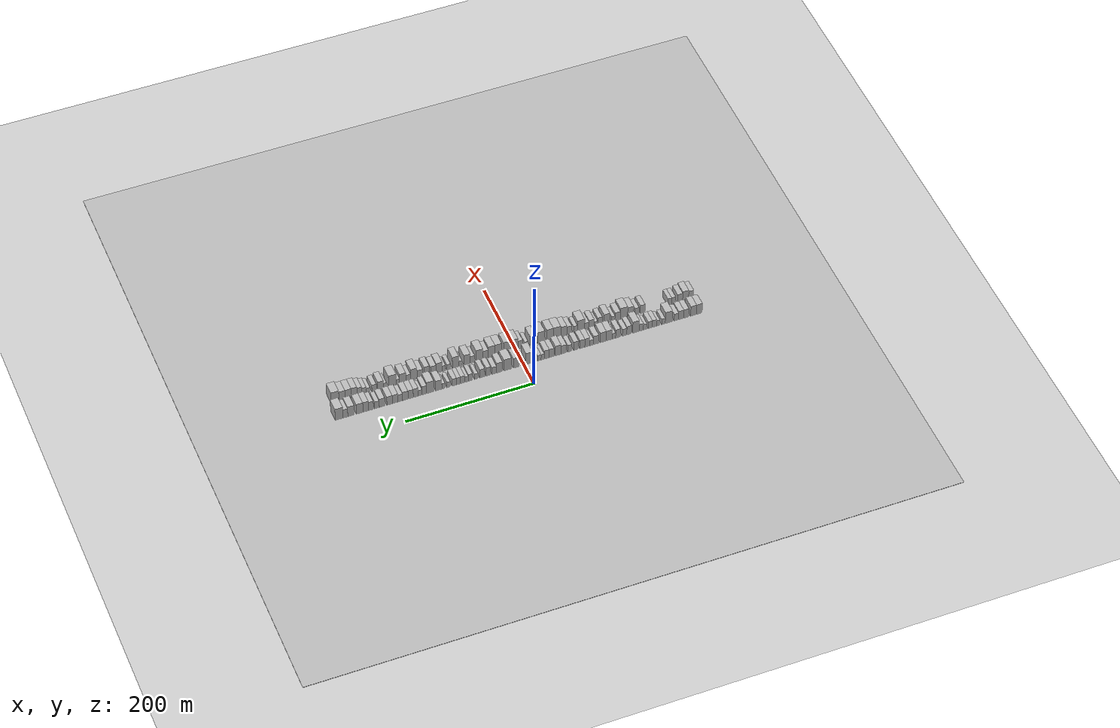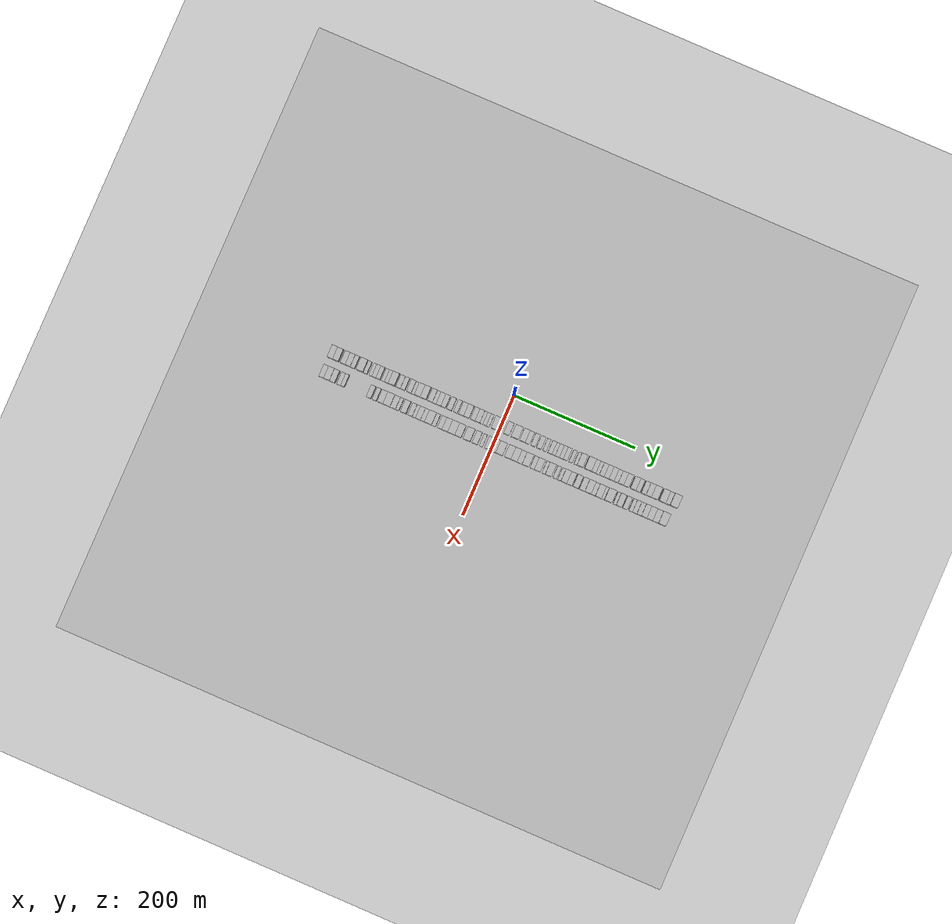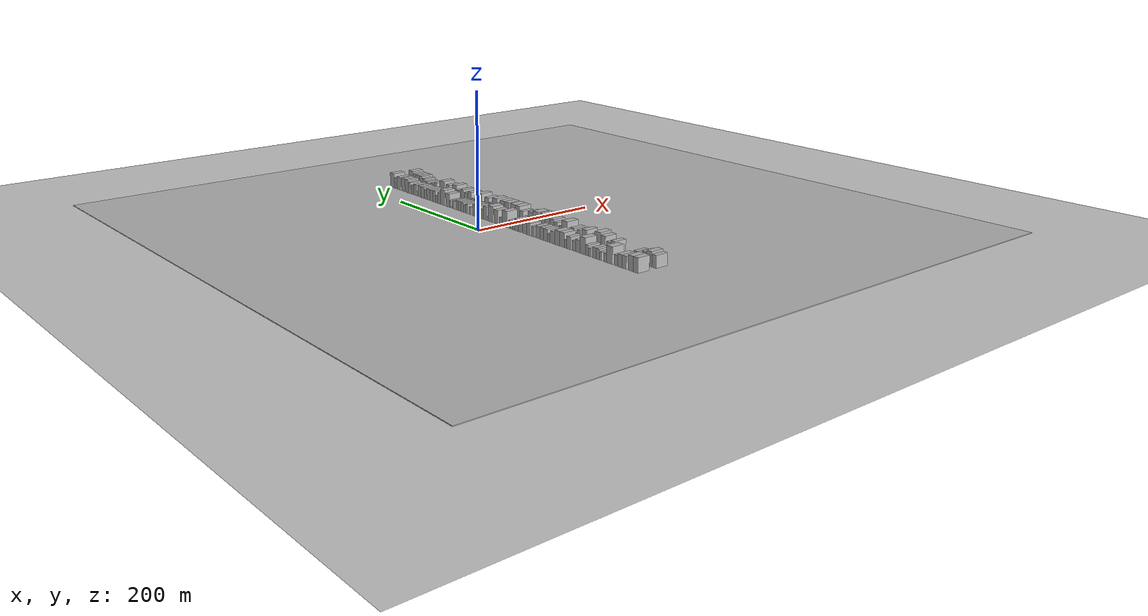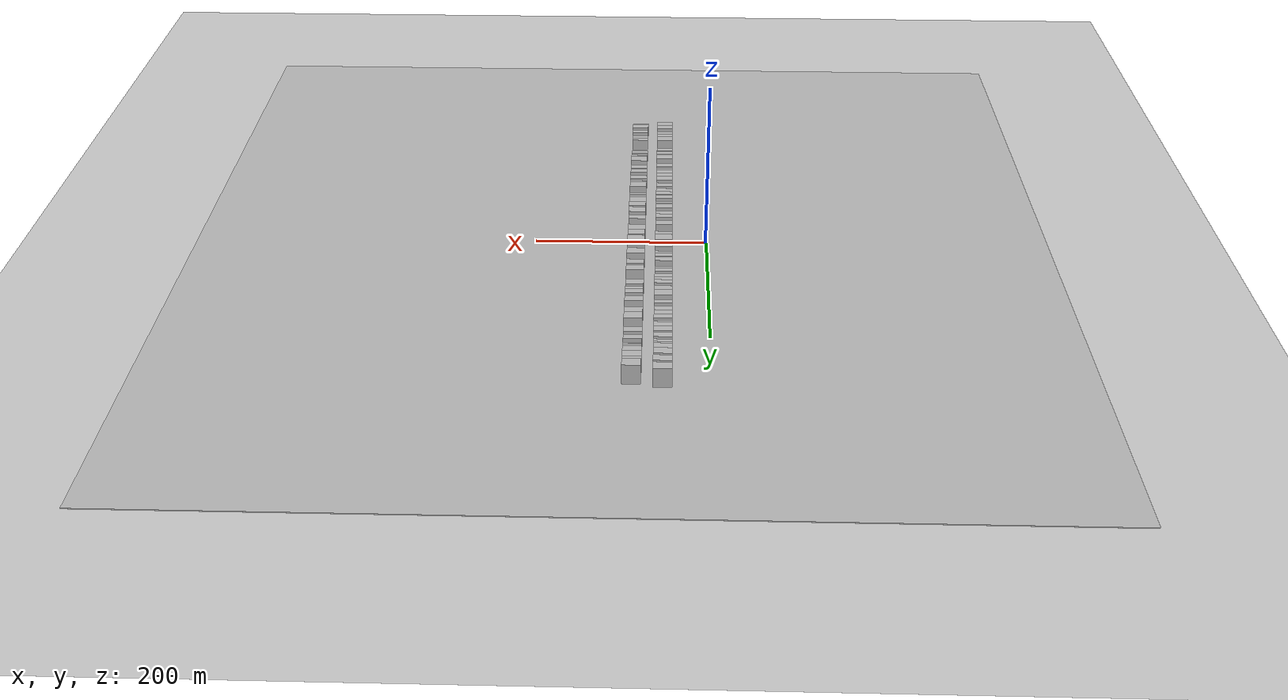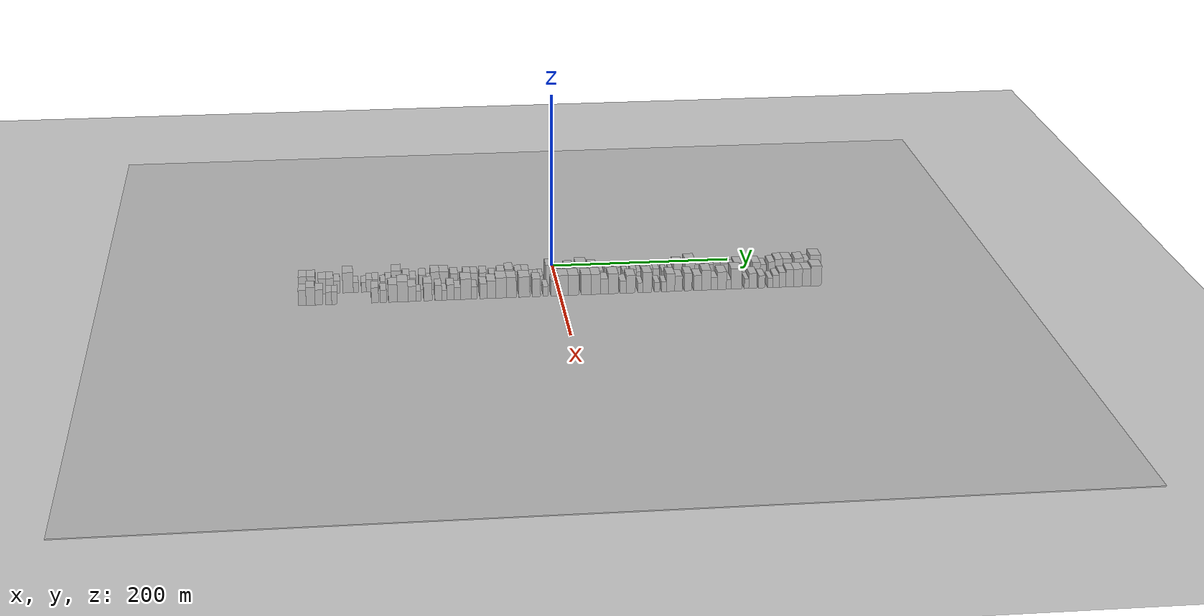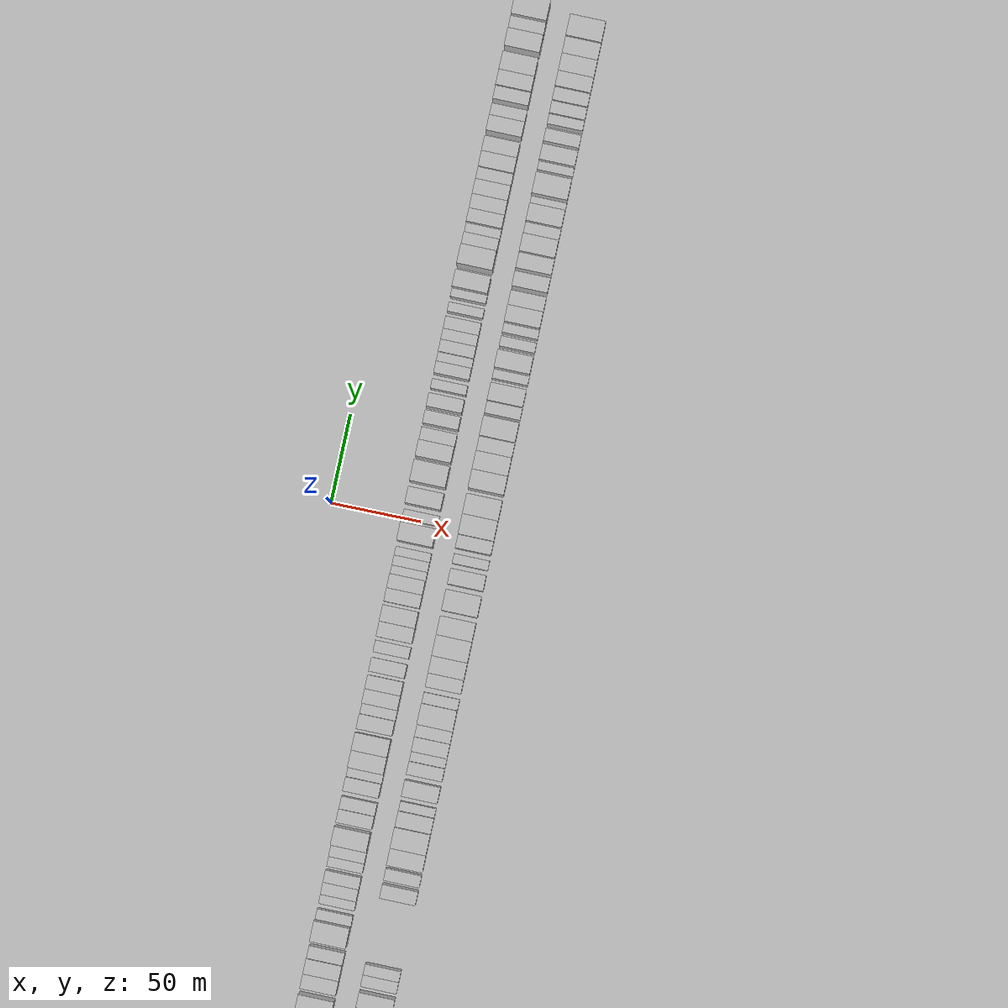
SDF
<?xml version="1.0" encoding="utf-8"?>

<sdf version="1.6">

   <world name="default">

      <gui fullscreen="0">

         <camera name="user_camera">

            <pose>-15 0 4.57585 0 0 0</pose>

            <view_controller>orbit</view_controller>

         </camera>

      </gui>

      <scene>

         <sky>

           <clouds>

             <speed>12</speed>

           </clouds>

         </sky>

         <ambient>0.4 0.4 0.4 1</ambient>

         <background>0.7 0.7 0.7 1</background>

         <shadows>1</shadows>

      </scene>

      <gravity>0 0 -9.8066</gravity>

      <magnetic_field>6e-06 2.3e-05 -4.2e-05</magnetic_field>

      <physics default="0" name="default_physics" type="ode">

         <ode>

            <solver>

               <type>quick</type>

               <iters>10</iters>

               <sor>1.0</sor>

               <use_dynamic_moi_rescaling>0</use_dynamic_moi_rescaling>

            </solver>

            <constraints>

               <cfm>0</cfm>

               <erp>0.2</erp>

               <contact_max_correcting_vel>100</contact_max_correcting_vel>

               <contact_surface_layer>0.001</contact_surface_layer>

            </constraints>

         </ode>

         <max_step_size>0.004</max_step_size>

         <real_time_factor>1</real_time_factor>

         <real_time_update_rate>250</real_time_update_rate>

      </physics>

      <light name="sun" type="directional">

         <cast_shadows>1</cast_shadows>

         <pose>0 0 10 0 0 0</pose>

         <diffuse>0.8 0.8 0.8 1</diffuse>

         <specular>0.2 0.2 0.2 1</specular>

         <attenuation>

            <range>1000</range>

            <constant>0.9</constant>

            <linear>0.01</linear>

            <quadratic>0.001</quadratic>

         </attenuation>

         <direction>-0.5 0.1 -0.9</direction>

      </light>

      <include>

         <name>ground_plane_1</name>

         <uri>model://HANNAS_ground_plane</uri>

         <pose>0 0 0  0 0 0</pose>

      </include>

      <include>

         <name>ground_plane_2</name>

         <uri>model://HANNAS_ground_plane</uri>

         <pose>100 0 0  0 0 0</pose>

      </include>

      <model name="building_1">

         <static>1</static>

         <pose frame="">50.0000 -279.3835 0 0.000000 0.000000 0.000000</pose>

         <link name="link">

            <pose frame="">0 0 10.50 0 0 0</pose>

            <collision name="collision">

               <geometry>

                  <box>

                     <size>20.0000 9.2331 21.0000</size>

                  </box>

               </geometry>

               <max_contacts>10</max_contacts>

               <surface>

                  <contact>

                     <ode/>

                  </contact>

                  <bounce/>

                  <friction>

                     <torsional>

                        <ode/>

                     </torsional>

                     <ode/>

                  </friction>

               </surface>

            </collision>

            <visual name="visual">

               <cast_shadows>0</cast_shadows>

               <geometry>

                  <box>

                     <size>20.0000 9.2331 21.0000</size>

                  </box>

               </geometry>

               <material>

                  <script>

                     <uri>model://HANNAS_wall/materials/scripts</uri>

                     <uri>model://HANNAS_wall/materials/textures</uri>

                     <name>vrc/HANNAS_wall</name>

                  </script>

               </material>

            </visual>

            <self_collide>0</self_collide>

            <enable_wind>0</enable_wind>

            <kinematic>0</kinematic>

         </link>

      </model>

      <model name="building_2">

         <static>1</static>

         <pose frame="">50.0000 -270.1055 0 0.000000 0.000000 0.000000</pose>

         <link name="link">

            <pose frame="">0 0 10.50 0 0 0</pose>

            <collision name="collision">

               <geometry>

                  <box>

                     <size>20.0000 9.3228 21.0000</size>

                  </box>

               </geometry>

               <max_contacts>10</max_contacts>

               <surface>

                  <contact>

                     <ode/>

                  </contact>

                  <bounce/>

                  <friction>

                     <torsional>

                        <ode/>

                     </torsional>

                     <ode/>

                  </friction>

               </surface>

            </collision>

            <visual name="visual">

               <cast_shadows>0</cast_shadows>

               <geometry>

                  <box>

                     <size>20.0000 9.3228 21.0000</size>

                  </box>

               </geometry>

               <material>

                  <script>

                     <uri>model://HANNAS_wall/materials/scripts</uri>

                     <uri>model://HANNAS_wall/materials/textures</uri>

                     <name>vrc/HANNAS_wall</name>

                  </script>

               </material>

            </visual>

            <self_collide>0</self_collide>

            <enable_wind>0</enable_wind>

            <kinematic>0</kinematic>

         </link>

      </model>

      <model name="building_3">

         <static>1</static>

         <pose frame="">50.0000 -258.4079 0 0.000000 0.000000 0.000000</pose>

         <link name="link">

            <pose frame="">0 0 9.00 0 0 0</pose>

            <collision name="collision">

               <geometry>

                  <box>

                     <size>20.0000 8.0726 18.0000</size>

                  </box>

               </geometry>

               <max_contacts>10</max_contacts>

               <surface>

                  <contact>

                     <ode/>

                  </contact>

                  <bounce/>

                  <friction>

                     <torsional>

                        <ode/>

                     </torsional>

                     <ode/>

                  </friction>

               </surface>

            </collision>

            <visual name="visual">

               <cast_shadows>0</cast_shadows>

               <geometry>

                  <box>

                     <size>20.0000 8.0726 18.0000</size>

                  </box>

               </geometry>

               <material>

                  <script>

                     <uri>model://HANNAS_wall/materials/scripts</uri>

                     <uri>model://HANNAS_wall/materials/textures</uri>

                     <name>vrc/HANNAS_wall</name>

                  </script>

               </material>

            </visual>

            <self_collide>0</self_collide>

            <enable_wind>0</enable_wind>

            <kinematic>0</kinematic>

         </link>

      </model>

      <model name="building_4">

         <static>1</static>

         <pose frame="">50.0000 -250.1520 0 0.000000 0.000000 0.000000</pose>

         <link name="link">

            <pose frame="">0 0 9.00 0 0 0</pose>

            <collision name="collision">

               <geometry>

                  <box>

                     <size>20.0000 8.4391 18.0000</size>

                  </box>

               </geometry>

               <max_contacts>10</max_contacts>

               <surface>

                  <contact>

                     <ode/>

                  </contact>

                  <bounce/>

                  <friction>

                     <torsional>

                        <ode/>

                     </torsional>

                     <ode/>

                  </friction>

               </surface>

            </collision>

            <visual name="visual">

               <cast_shadows>0</cast_shadows>

               <geometry>

                  <box>

                     <size>20.0000 8.4391 18.0000</size>

                  </box>

               </geometry>

               <material>

                  <script>

                     <uri>model://HANNAS_wall/materials/scripts</uri>

                     <uri>model://HANNAS_wall/materials/textures</uri>

                     <name>vrc/HANNAS_wall</name>

                  </script>

               </material>

            </visual>

            <self_collide>0</self_collide>

            <enable_wind>0</enable_wind>

            <kinematic>0</kinematic>

         </link>

      </model>

      <model name="building_5">

         <static>1</static>

         <pose frame="">50.0000 -242.4353 0 0.000000 0.000000 0.000000</pose>

         <link name="link">

            <pose frame="">0 0 7.50 0 0 0</pose>

            <collision name="collision">

               <geometry>

                  <box>

                     <size>20.0000 6.9945 15.0000</size>

                  </box>

               </geometry>

               <max_contacts>10</max_contacts>

               <surface>

                  <contact>

                     <ode/>

                  </contact>

                  <bounce/>

                  <friction>

                     <torsional>

                        <ode/>

                     </torsional>

                     <ode/>

                  </friction>

               </surface>

            </collision>

            <visual name="visual">

               <cast_shadows>0</cast_shadows>

               <geometry>

                  <box>

                     <size>20.0000 6.9945 15.0000</size>

                  </box>

               </geometry>

               <material>

                  <script>

                     <uri>model://HANNAS_wall/materials/scripts</uri>

                     <uri>model://HANNAS_wall/materials/textures</uri>

                     <name>vrc/HANNAS_wall</name>

                  </script>

               </material>

            </visual>

            <self_collide>0</self_collide>

            <enable_wind>0</enable_wind>

            <kinematic>0</kinematic>

         </link>

      </model>

      <model name="building_6">

         <static>1</static>

         <pose frame="">50.0000 -230.2400 0 0.000000 0.000000 0.000000</pose>

         <link name="link">

            <pose frame="">0 0 12.00 0 0 0</pose>

            <collision name="collision">

               <geometry>

                  <box>

                     <size>20.0000 11.3961 24.0000</size>

                  </box>

               </geometry>

               <max_contacts>10</max_contacts>

               <surface>

                  <contact>

                     <ode/>

                  </contact>

                  <bounce/>

                  <friction>

                     <torsional>

                        <ode/>

                     </torsional>

                     <ode/>

                  </friction>

               </surface>

            </collision>

            <visual name="visual">

               <cast_shadows>0</cast_shadows>

               <geometry>

                  <box>

                     <size>20.0000 11.3961 24.0000</size>

                  </box>

               </geometry>

               <material>

                  <script>

                     <uri>model://HANNAS_wall/materials/scripts</uri>

                     <uri>model://HANNAS_wall/materials/textures</uri>

                     <name>vrc/HANNAS_wall</name>

                  </script>

               </material>

            </visual>

            <self_collide>0</self_collide>

            <enable_wind>0</enable_wind>

            <kinematic>0</kinematic>

         </link>

      </model>

      <model name="building_7">

         <static>1</static>

         <pose frame="">50.0000 -221.6460 0 0.000000 0.000000 0.000000</pose>

         <link name="link">

            <pose frame="">0 0 6.00 0 0 0</pose>

            <collision name="collision">

               <geometry>

                  <box>

                     <size>20.0000 5.7920 12.0000</size>

                  </box>

               </geometry>

               <max_contacts>10</max_contacts>

               <surface>

                  <contact>

                     <ode/>

                  </contact>

                  <bounce/>

                  <friction>

                     <torsional>

                        <ode/>

                     </torsional>

                     <ode/>

                  </friction>

               </surface>

            </collision>

            <visual name="visual">

               <cast_shadows>0</cast_shadows>

               <geometry>

                  <box>

                     <size>20.0000 5.7920 12.0000</size>

                  </box>

               </geometry>

               <material>

                  <script>

                     <uri>model://HANNAS_wall/materials/scripts</uri>

                     <uri>model://HANNAS_wall/materials/textures</uri>

                     <name>vrc/HANNAS_wall</name>

                  </script>

               </material>

            </visual>

            <self_collide>0</self_collide>

            <enable_wind>0</enable_wind>

            <kinematic>0</kinematic>

         </link>

      </model>

      <model name="building_8">

         <static>1</static>

         <pose frame="">50.0000 -213.1121 0 0.000000 0.000000 0.000000</pose>

         <link name="link">

            <pose frame="">0 0 6.00 0 0 0</pose>

            <collision name="collision">

               <geometry>

                  <box>

                     <size>20.0000 5.2758 12.0000</size>

                  </box>

               </geometry>

               <max_contacts>10</max_contacts>

               <surface>

                  <contact>

                     <ode/>

                  </contact>

                  <bounce/>

                  <friction>

                     <torsional>

                        <ode/>

                     </torsional>

                     <ode/>

                  </friction>

               </surface>

            </collision>

            <visual name="visual">

               <cast_shadows>0</cast_shadows>

               <geometry>

                  <box>

                     <size>20.0000 5.2758 12.0000</size>

                  </box>

               </geometry>

               <material>

                  <script>

                     <uri>model://HANNAS_wall/materials/scripts</uri>

                     <uri>model://HANNAS_wall/materials/textures</uri>

                     <name>vrc/HANNAS_wall</name>

                  </script>

               </material>

            </visual>

            <self_collide>0</self_collide>

            <enable_wind>0</enable_wind>

            <kinematic>0</kinematic>

         </link>

      </model>

      <model name="building_9">

         <static>1</static>

         <pose frame="">50.0000 -207.1385 0 0.000000 0.000000 0.000000</pose>

         <link name="link">

            <pose frame="">0 0 7.50 0 0 0</pose>

            <collision name="collision">

               <geometry>

                  <box>

                     <size>20.0000 6.6714 15.0000</size>

                  </box>

               </geometry>

               <max_contacts>10</max_contacts>

               <surface>

                  <contact>

                     <ode/>

                  </contact>

                  <bounce/>

                  <friction>

                     <torsional>

                        <ode/>

                     </torsional>

                     <ode/>

                  </friction>

               </surface>

            </collision>

            <visual name="visual">

               <cast_shadows>0</cast_shadows>

               <geometry>

                  <box>

                     <size>20.0000 6.6714 15.0000</size>

                  </box>

               </geometry>

               <material>

                  <script>

                     <uri>model://HANNAS_wall/materials/scripts</uri>

                     <uri>model://HANNAS_wall/materials/textures</uri>

                     <name>vrc/HANNAS_wall</name>

                  </script>

               </material>

            </visual>

            <self_collide>0</self_collide>

            <enable_wind>0</enable_wind>

            <kinematic>0</kinematic>

         </link>

      </model>

      <model name="building_10">

         <static>1</static>

         <pose frame="">50.0000 -200.4387 0 0.000000 0.000000 0.000000</pose>

         <link name="link">

            <pose frame="">0 0 7.50 0 0 0</pose>

            <collision name="collision">

               <geometry>

                  <box>

                     <size>20.0000 6.7280 15.0000</size>

                  </box>

               </geometry>

               <max_contacts>10</max_contacts>

               <surface>

                  <contact>

                     <ode/>

                  </contact>

                  <bounce/>

                  <friction>

                     <torsional>

                        <ode/>

                     </torsional>

                     <ode/>

                  </friction>

               </surface>

            </collision>

            <visual name="visual">

               <cast_shadows>0</cast_shadows>

               <geometry>

                  <box>

                     <size>20.0000 6.7280 15.0000</size>

                  </box>

               </geometry>

               <material>

                  <script>

                     <uri>model://HANNAS_wall/materials/scripts</uri>

                     <uri>model://HANNAS_wall/materials/textures</uri>

                     <name>vrc/HANNAS_wall</name>

                  </script>

               </material>

            </visual>

            <self_collide>0</self_collide>

            <enable_wind>0</enable_wind>

            <kinematic>0</kinematic>

         </link>

      </model>

      <model name="building_11">

         <static>1</static>

         <pose frame="">50.0000 -192.2486 0 0.000000 0.000000 0.000000</pose>

         <link name="link">

            <pose frame="">0 0 6.00 0 0 0</pose>

            <collision name="collision">

               <geometry>

                  <box>

                     <size>20.0000 5.6523 12.0000</size>

                  </box>

               </geometry>

               <max_contacts>10</max_contacts>

               <surface>

                  <contact>

                     <ode/>

                  </contact>

                  <bounce/>

                  <friction>

                     <torsional>

                        <ode/>

                     </torsional>

                     <ode/>

                  </friction>

               </surface>

            </collision>

            <visual name="visual">

               <cast_shadows>0</cast_shadows>

               <geometry>

                  <box>

                     <size>20.0000 5.6523 12.0000</size>

                  </box>

               </geometry>

               <material>

                  <script>

                     <uri>model://HANNAS_wall/materials/scripts</uri>

                     <uri>model://HANNAS_wall/materials/textures</uri>

                     <name>vrc/HANNAS_wall</name>

                  </script>

               </material>

            </visual>

            <self_collide>0</self_collide>

            <enable_wind>0</enable_wind>

            <kinematic>0</kinematic>

         </link>

      </model>

      <model name="building_12">

         <static>1</static>

         <pose frame="">50.0000 -186.0537 0 0.000000 0.000000 0.000000</pose>

         <link name="link">

            <pose frame="">0 0 7.50 0 0 0</pose>

            <collision name="collision">

               <geometry>

                  <box>

                     <size>20.0000 6.7374 15.0000</size>

                  </box>

               </geometry>

               <max_contacts>10</max_contacts>

               <surface>

                  <contact>

                     <ode/>

                  </contact>

                  <bounce/>

                  <friction>

                     <torsional>

                        <ode/>

                     </torsional>

                     <ode/>

                  </friction>

               </surface>

            </collision>

            <visual name="visual">

               <cast_shadows>0</cast_shadows>

               <geometry>

                  <box>

                     <size>20.0000 6.7374 15.0000</size>

                  </box>

               </geometry>

               <material>

                  <script>

                     <uri>model://HANNAS_wall/materials/scripts</uri>

                     <uri>model://HANNAS_wall/materials/textures</uri>

                     <name>vrc/HANNAS_wall</name>

                  </script>

               </material>

            </visual>

            <self_collide>0</self_collide>

            <enable_wind>0</enable_wind>

            <kinematic>0</kinematic>

         </link>

      </model>

      <model name="building_13">

         <static>1</static>

         <pose frame="">50.0000 -177.5244 0 0.000000 0.000000 0.000000</pose>

         <link name="link">

            <pose frame="">0 0 12.00 0 0 0</pose>

            <collision name="collision">

               <geometry>

                  <box>

                     <size>20.0000 10.3212 24.0000</size>

                  </box>

               </geometry>

               <max_contacts>10</max_contacts>

               <surface>

                  <contact>

                     <ode/>

                  </contact>

                  <bounce/>

                  <friction>

                     <torsional>

                        <ode/>

                     </torsional>

                     <ode/>

                  </friction>

               </surface>

            </collision>

            <visual name="visual">

               <cast_shadows>0</cast_shadows>

               <geometry>

                  <box>

                     <size>20.0000 10.3212 24.0000</size>

                  </box>

               </geometry>

               <material>

                  <script>

                     <uri>model://HANNAS_wall/materials/scripts</uri>

                     <uri>model://HANNAS_wall/materials/textures</uri>

                     <name>vrc/HANNAS_wall</name>

                  </script>

               </material>

            </visual>

            <self_collide>0</self_collide>

            <enable_wind>0</enable_wind>

            <kinematic>0</kinematic>

         </link>

      </model>

      <model name="building_14">

         <static>1</static>

         <pose frame="">50.0000 -166.6423 0 0.000000 0.000000 0.000000</pose>

         <link name="link">

            <pose frame="">0 0 9.00 0 0 0</pose>

            <collision name="collision">

               <geometry>

                  <box>

                     <size>20.0000 7.4430 18.0000</size>

                  </box>

               </geometry>

               <max_contacts>10</max_contacts>

               <surface>

                  <contact>

                     <ode/>

                  </contact>

                  <bounce/>

                  <friction>

                     <torsional>

                        <ode/>

                     </torsional>

                     <ode/>

                  </friction>

               </surface>

            </collision>

            <visual name="visual">

               <cast_shadows>0</cast_shadows>

               <geometry>

                  <box>

                     <size>20.0000 7.4430 18.0000</size>

                  </box>

               </geometry>

               <material>

                  <script>

                     <uri>model://HANNAS_wall/materials/scripts</uri>

                     <uri>model://HANNAS_wall/materials/textures</uri>

                     <name>vrc/HANNAS_wall</name>

                  </script>

               </material>

            </visual>

            <self_collide>0</self_collide>

            <enable_wind>0</enable_wind>

            <kinematic>0</kinematic>

         </link>

      </model>

      <model name="building_15">

         <static>1</static>

         <pose frame="">50.0000 -159.3903 0 0.000000 0.000000 0.000000</pose>

         <link name="link">

            <pose frame="">0 0 7.50 0 0 0</pose>

            <collision name="collision">

               <geometry>

                  <box>

                     <size>20.0000 7.0609 15.0000</size>

                  </box>

               </geometry>

               <max_contacts>10</max_contacts>

               <surface>

                  <contact>

                     <ode/>

                  </contact>

                  <bounce/>

                  <friction>

                     <torsional>

                        <ode/>

                     </torsional>

                     <ode/>

                  </friction>

               </surface>

            </collision>

            <visual name="visual">

               <cast_shadows>0</cast_shadows>

               <geometry>

                  <box>

                     <size>20.0000 7.0609 15.0000</size>

                  </box>

               </geometry>

               <material>

                  <script>

                     <uri>model://HANNAS_wall/materials/scripts</uri>

                     <uri>model://HANNAS_wall/materials/textures</uri>

                     <name>vrc/HANNAS_wall</name>

                  </script>

               </material>

            </visual>

            <self_collide>0</self_collide>

            <enable_wind>0</enable_wind>

            <kinematic>0</kinematic>

         </link>

      </model>

      <model name="building_16">

         <static>1</static>

         <pose frame="">50.0000 -148.9414 0 0.000000 0.000000 0.000000</pose>

         <link name="link">

            <pose frame="">0 0 9.00 0 0 0</pose>

            <collision name="collision">

               <geometry>

                  <box>

                     <size>20.0000 7.8368 18.0000</size>

                  </box>

               </geometry>

               <max_contacts>10</max_contacts>

               <surface>

                  <contact>

                     <ode/>

                  </contact>

                  <bounce/>

                  <friction>

                     <torsional>

                        <ode/>

                     </torsional>

                     <ode/>

                  </friction>

               </surface>

            </collision>

            <visual name="visual">

               <cast_shadows>0</cast_shadows>

               <geometry>

                  <box>

                     <size>20.0000 7.8368 18.0000</size>

                  </box>

               </geometry>

               <material>

                  <script>

                     <uri>model://HANNAS_wall/materials/scripts</uri>

                     <uri>model://HANNAS_wall/materials/textures</uri>

                     <name>vrc/HANNAS_wall</name>

                  </script>

               </material>

            </visual>

            <self_collide>0</self_collide>

            <enable_wind>0</enable_wind>

            <kinematic>0</kinematic>

         </link>

      </model>

      <model name="building_17">

         <static>1</static>

         <pose frame="">50.0000 -142.3813 0 0.000000 0.000000 0.000000</pose>

         <link name="link">

            <pose frame="">0 0 6.00 0 0 0</pose>

            <collision name="collision">

               <geometry>

                  <box>

                     <size>20.0000 5.2835 12.0000</size>

                  </box>

               </geometry>

               <max_contacts>10</max_contacts>

               <surface>

                  <contact>

                     <ode/>

                  </contact>

                  <bounce/>

                  <friction>

                     <torsional>

                        <ode/>

                     </torsional>

                     <ode/>

                  </friction>

               </surface>

            </collision>

            <visual name="visual">

               <cast_shadows>0</cast_shadows>

               <geometry>

                  <box>

                     <size>20.0000 5.2835 12.0000</size>

                  </box>

               </geometry>

               <material>

                  <script>

                     <uri>model://HANNAS_wall/materials/scripts</uri>

                     <uri>model://HANNAS_wall/materials/textures</uri>

                     <name>vrc/HANNAS_wall</name>

                  </script>

               </material>

            </visual>

            <self_collide>0</self_collide>

            <enable_wind>0</enable_wind>

            <kinematic>0</kinematic>

         </link>

      </model>

      <model name="building_18">

         <static>1</static>

         <pose frame="">50.0000 -134.9490 0 0.000000 0.000000 0.000000</pose>

         <link name="link">

            <pose frame="">0 0 10.50 0 0 0</pose>

            <collision name="collision">

               <geometry>

                  <box>

                     <size>20.0000 9.5811 21.0000</size>

                  </box>

               </geometry>

               <max_contacts>10</max_contacts>

               <surface>

                  <contact>

                     <ode/>

                  </contact>

                  <bounce/>

                  <friction>

                     <torsional>

                        <ode/>

                     </torsional>

                     <ode/>

                  </friction>

               </surface>

            </collision>

            <visual name="visual">

               <cast_shadows>0</cast_shadows>

               <geometry>

                  <box>

                     <size>20.0000 9.5811 21.0000</size>

                  </box>

               </geometry>

               <material>

                  <script>

                     <uri>model://HANNAS_wall/materials/scripts</uri>

                     <uri>model://HANNAS_wall/materials/textures</uri>

                     <name>vrc/HANNAS_wall</name>

                  </script>

               </material>

            </visual>

            <self_collide>0</self_collide>

            <enable_wind>0</enable_wind>

            <kinematic>0</kinematic>

         </link>

      </model>

      <model name="building_19">

         <static>1</static>

         <pose frame="">50.0000 -125.2117 0 0.000000 0.000000 0.000000</pose>

         <link name="link">

            <pose frame="">0 0 10.50 0 0 0</pose>

            <collision name="collision">

               <geometry>

                  <box>

                     <size>20.0000 9.8934 21.0000</size>

                  </box>

               </geometry>

               <max_contacts>10</max_contacts>

               <surface>

                  <contact>

                     <ode/>

                  </contact>

                  <bounce/>

                  <friction>

                     <torsional>

                        <ode/>

                     </torsional>

                     <ode/>

                  </friction>

               </surface>

            </collision>

            <visual name="visual">

               <cast_shadows>0</cast_shadows>

               <geometry>

                  <box>

                     <size>20.0000 9.8934 21.0000</size>

                  </box>

               </geometry>

               <material>

                  <script>

                     <uri>model://HANNAS_wall/materials/scripts</uri>

                     <uri>model://HANNAS_wall/materials/textures</uri>

                     <name>vrc/HANNAS_wall</name>

                  </script>

               </material>

            </visual>

            <self_collide>0</self_collide>

            <enable_wind>0</enable_wind>

            <kinematic>0</kinematic>

         </link>

      </model>

      <model name="building_20">

         <static>1</static>

         <pose frame="">50.0000 -114.0749 0 0.000000 0.000000 0.000000</pose>

         <link name="link">

            <pose frame="">0 0 9.00 0 0 0</pose>

            <collision name="collision">

               <geometry>

                  <box>

                     <size>20.0000 8.3802 18.0000</size>

                  </box>

               </geometry>

               <max_contacts>10</max_contacts>

               <surface>

                  <contact>

                     <ode/>

                  </contact>

                  <bounce/>

                  <friction>

                     <torsional>

                        <ode/>

                     </torsional>

                     <ode/>

                  </friction>

               </surface>

            </collision>

            <visual name="visual">

               <cast_shadows>0</cast_shadows>

               <geometry>

                  <box>

                     <size>20.0000 8.3802 18.0000</size>

                  </box>

               </geometry>

               <material>

                  <script>

                     <uri>model://HANNAS_wall/materials/scripts</uri>

                     <uri>model://HANNAS_wall/materials/textures</uri>

                     <name>vrc/HANNAS_wall</name>

                  </script>

               </material>

            </visual>

            <self_collide>0</self_collide>

            <enable_wind>0</enable_wind>

            <kinematic>0</kinematic>

         </link>

      </model>

      <model name="building_21">

         <static>1</static>

         <pose frame="">50.0000 -106.9440 0 0.000000 0.000000 0.000000</pose>

         <link name="link">

            <pose frame="">0 0 6.00 0 0 0</pose>

            <collision name="collision">

               <geometry>

                  <box>

                     <size>20.0000 5.8816 12.0000</size>

                  </box>

               </geometry>

               <max_contacts>10</max_contacts>

               <surface>

                  <contact>

                     <ode/>

                  </contact>

                  <bounce/>

                  <friction>

                     <torsional>

                        <ode/>

                     </torsional>

                     <ode/>

                  </friction>

               </surface>

            </collision>

            <visual name="visual">

               <cast_shadows>0</cast_shadows>

               <geometry>

                  <box>

                     <size>20.0000 5.8816 12.0000</size>

                  </box>

               </geometry>

               <material>

                  <script>

                     <uri>model://HANNAS_wall/materials/scripts</uri>

                     <uri>model://HANNAS_wall/materials/textures</uri>

                     <name>vrc/HANNAS_wall</name>

                  </script>

               </material>

            </visual>

            <self_collide>0</self_collide>

            <enable_wind>0</enable_wind>

            <kinematic>0</kinematic>

         </link>

      </model>

      <model name="building_22">

         <static>1</static>

         <pose frame="">50.0000 -99.9603 0 0.000000 0.000000 0.000000</pose>

         <link name="link">

            <pose frame="">0 0 9.00 0 0 0</pose>

            <collision name="collision">

               <geometry>

                  <box>

                     <size>20.0000 8.0857 18.0000</size>

                  </box>

               </geometry>

               <max_contacts>10</max_contacts>

               <surface>

                  <contact>

                     <ode/>

                  </contact>

                  <bounce/>

                  <friction>

                     <torsional>

                        <ode/>

                     </torsional>

                     <ode/>

                  </friction>

               </surface>

            </collision>

            <visual name="visual">

               <cast_shadows>0</cast_shadows>

               <geometry>

                  <box>

                     <size>20.0000 8.0857 18.0000</size>

                  </box>

               </geometry>

               <material>

                  <script>

                     <uri>model://HANNAS_wall/materials/scripts</uri>

                     <uri>model://HANNAS_wall/materials/textures</uri>

                     <name>vrc/HANNAS_wall</name>

                  </script>

               </material>

            </visual>

            <self_collide>0</self_collide>

            <enable_wind>0</enable_wind>

            <kinematic>0</kinematic>

         </link>

      </model>

      <model name="building_23">

         <static>1</static>

         <pose frame="">50.0000 -92.0587 0 0.000000 0.000000 0.000000</pose>

         <link name="link">

            <pose frame="">0 0 9.00 0 0 0</pose>

            <collision name="collision">

               <geometry>

                  <box>

                     <size>20.0000 7.7175 18.0000</size>

                  </box>

               </geometry>

               <max_contacts>10</max_contacts>

               <surface>

                  <contact>

                     <ode/>

                  </contact>

                  <bounce/>

                  <friction>

                     <torsional>

                        <ode/>

                     </torsional>

                     <ode/>

                  </friction>

               </surface>

            </collision>

            <visual name="visual">

               <cast_shadows>0</cast_shadows>

               <geometry>

                  <box>

                     <size>20.0000 7.7175 18.0000</size>

                  </box>

               </geometry>

               <material>

                  <script>

                     <uri>model://HANNAS_wall/materials/scripts</uri>

                     <uri>model://HANNAS_wall/materials/textures</uri>

                     <name>vrc/HANNAS_wall</name>

                  </script>

               </material>

            </visual>

            <self_collide>0</self_collide>

            <enable_wind>0</enable_wind>

            <kinematic>0</kinematic>

         </link>

      </model>

      <model name="building_24">

         <static>1</static>

         <pose frame="">50.0000 -82.2787 0 0.000000 0.000000 0.000000</pose>

         <link name="link">

            <pose frame="">0 0 9.00 0 0 0</pose>

            <collision name="collision">

               <geometry>

                  <box>

                     <size>20.0000 7.8427 18.0000</size>

                  </box>

               </geometry>

               <max_contacts>10</max_contacts>

               <surface>

                  <contact>

                     <ode/>

                  </contact>

                  <bounce/>

                  <friction>

                     <torsional>

                        <ode/>

                     </torsional>

                     <ode/>

                  </friction>

               </surface>

            </collision>

            <visual name="visual">

               <cast_shadows>0</cast_shadows>

               <geometry>

                  <box>

                     <size>20.0000 7.8427 18.0000</size>

                  </box>

               </geometry>

               <material>

                  <script>

                     <uri>model://HANNAS_wall/materials/scripts</uri>

                     <uri>model://HANNAS_wall/materials/textures</uri>

                     <name>vrc/HANNAS_wall</name>

                  </script>

               </material>

            </visual>

            <self_collide>0</self_collide>

            <enable_wind>0</enable_wind>

            <kinematic>0</kinematic>

         </link>

      </model>

      <model name="building_25">

         <static>1</static>

         <pose frame="">50.0000 -72.0794 0 0.000000 0.000000 0.000000</pose>

         <link name="link">

            <pose frame="">0 0 7.50 0 0 0</pose>

            <collision name="collision">

               <geometry>

                  <box>

                     <size>20.0000 6.5558 15.0000</size>

                  </box>

               </geometry>

               <max_contacts>10</max_contacts>

               <surface>

                  <contact>

                     <ode/>

                  </contact>

                  <bounce/>

                  <friction>

                     <torsional>

                        <ode/>

                     </torsional>

                     <ode/>

                  </friction>

               </surface>

            </collision>

            <visual name="visual">

               <cast_shadows>0</cast_shadows>

               <geometry>

                  <box>

                     <size>20.0000 6.5558 15.0000</size>

                  </box>

               </geometry>

               <material>

                  <script>

                     <uri>model://HANNAS_wall/materials/scripts</uri>

                     <uri>model://HANNAS_wall/materials/textures</uri>

                     <name>vrc/HANNAS_wall</name>

                  </script>

               </material>

            </visual>

            <self_collide>0</self_collide>

            <enable_wind>0</enable_wind>

            <kinematic>0</kinematic>

         </link>

      </model>

      <model name="building_26">

         <static>1</static>

         <pose frame="">50.0000 -62.5581 0 0.000000 0.000000 0.000000</pose>

         <link name="link">

            <pose frame="">0 0 9.00 0 0 0</pose>

            <collision name="collision">

               <geometry>

                  <box>

                     <size>20.0000 8.4868 18.0000</size>

                  </box>

               </geometry>

               <max_contacts>10</max_contacts>

               <surface>

                  <contact>

                     <ode/>

                  </contact>

                  <bounce/>

                  <friction>

                     <torsional>

                        <ode/>

                     </torsional>

                     <ode/>

                  </friction>

               </surface>

            </collision>

            <visual name="visual">

               <cast_shadows>0</cast_shadows>

               <geometry>

                  <box>

                     <size>20.0000 8.4868 18.0000</size>

                  </box>

               </geometry>

               <material>

                  <script>

                     <uri>model://HANNAS_wall/materials/scripts</uri>

                     <uri>model://HANNAS_wall/materials/textures</uri>

                     <name>vrc/HANNAS_wall</name>

                  </script>

               </material>

            </visual>

            <self_collide>0</self_collide>

            <enable_wind>0</enable_wind>

            <kinematic>0</kinematic>

         </link>

      </model>

      <model name="building_27">

         <static>1</static>

         <pose frame="">50.0000 -53.7057 0 0.000000 0.000000 0.000000</pose>

         <link name="link">

            <pose frame="">0 0 10.50 0 0 0</pose>

            <collision name="collision">

               <geometry>

                  <box>

                     <size>20.0000 9.2180 21.0000</size>

                  </box>

               </geometry>

               <max_contacts>10</max_contacts>

               <surface>

                  <contact>

                     <ode/>

                  </contact>

                  <bounce/>

                  <friction>

                     <torsional>

                        <ode/>

                     </torsional>

                     <ode/>

                  </friction>

               </surface>

            </collision>

            <visual name="visual">

               <cast_shadows>0</cast_shadows>

               <geometry>

                  <box>

                     <size>20.0000 9.2180 21.0000</size>

                  </box>

               </geometry>

               <material>

                  <script>

                     <uri>model://HANNAS_wall/materials/scripts</uri>

                     <uri>model://HANNAS_wall/materials/textures</uri>

                     <name>vrc/HANNAS_wall</name>

                  </script>

               </material>

            </visual>

            <self_collide>0</self_collide>

            <enable_wind>0</enable_wind>

            <kinematic>0</kinematic>

         </link>

      </model>

      <model name="building_28">

         <static>1</static>

         <pose frame="">50.0000 -43.3531 0 0.000000 0.000000 0.000000</pose>

         <link name="link">

            <pose frame="">0 0 9.00 0 0 0</pose>

            <collision name="collision">

               <geometry>

                  <box>

                     <size>20.0000 7.4873 18.0000</size>

                  </box>

               </geometry>

               <max_contacts>10</max_contacts>

               <surface>

                  <contact>

                     <ode/>

                  </contact>

                  <bounce/>

                  <friction>

                     <torsional>

                        <ode/>

                     </torsional>

                     <ode/>

                  </friction>

               </surface>

            </collision>

            <visual name="visual">

               <cast_shadows>0</cast_shadows>

               <geometry>

                  <box>

                     <size>20.0000 7.4873 18.0000</size>

                  </box>

               </geometry>

               <material>

                  <script>

                     <uri>model://HANNAS_wall/materials/scripts</uri>

                     <uri>model://HANNAS_wall/materials/textures</uri>

                     <name>vrc/HANNAS_wall</name>

                  </script>

               </material>

            </visual>

            <self_collide>0</self_collide>

            <enable_wind>0</enable_wind>

            <kinematic>0</kinematic>

         </link>

      </model>

      <model name="building_29">

         <static>1</static>

         <pose frame="">50.0000 -35.6290 0 0.000000 0.000000 0.000000</pose>

         <link name="link">

            <pose frame="">0 0 9.00 0 0 0</pose>

            <collision name="collision">

               <geometry>

                  <box>

                     <size>20.0000 7.9609 18.0000</size>

                  </box>

               </geometry>

               <max_contacts>10</max_contacts>

               <surface>

                  <contact>

                     <ode/>

                  </contact>

                  <bounce/>

                  <friction>

                     <torsional>

                        <ode/>

                     </torsional>

                     <ode/>

                  </friction>

               </surface>

            </collision>

            <visual name="visual">

               <cast_shadows>0</cast_shadows>

               <geometry>

                  <box>

                     <size>20.0000 7.9609 18.0000</size>

                  </box>

               </geometry>

               <material>

                  <script>

                     <uri>model://HANNAS_wall/materials/scripts</uri>

                     <uri>model://HANNAS_wall/materials/textures</uri>

                     <name>vrc/HANNAS_wall</name>

                  </script>

               </material>

            </visual>

            <self_collide>0</self_collide>

            <enable_wind>0</enable_wind>

            <kinematic>0</kinematic>

         </link>

      </model>

      <model name="building_30">

         <static>1</static>

         <pose frame="">50.0000 -29.1863 0 0.000000 0.000000 0.000000</pose>

         <link name="link">

            <pose frame="">0 0 6.00 0 0 0</pose>

            <collision name="collision">

               <geometry>

                  <box>

                     <size>20.0000 4.9245 12.0000</size>

                  </box>

               </geometry>

               <max_contacts>10</max_contacts>

               <surface>

                  <contact>

                     <ode/>

                  </contact>

                  <bounce/>

                  <friction>

                     <torsional>

                        <ode/>

                     </torsional>

                     <ode/>

                  </friction>

               </surface>

            </collision>

            <visual name="visual">

               <cast_shadows>0</cast_shadows>

               <geometry>

                  <box>

                     <size>20.0000 4.9245 12.0000</size>

                  </box>

               </geometry>

               <material>

                  <script>

                     <uri>model://HANNAS_wall/materials/scripts</uri>

                     <uri>model://HANNAS_wall/materials/textures</uri>

                     <name>vrc/HANNAS_wall</name>

                  </script>

               </material>

            </visual>

            <self_collide>0</self_collide>

            <enable_wind>0</enable_wind>

            <kinematic>0</kinematic>

         </link>

      </model>

      <model name="building_31">

         <static>1</static>

         <pose frame="">50.0000 -23.9347 0 0.000000 0.000000 0.000000</pose>

         <link name="link">

            <pose frame="">0 0 6.00 0 0 0</pose>

            <collision name="collision">

               <geometry>

                  <box>

                     <size>20.0000 5.5786 12.0000</size>

                  </box>

               </geometry>

               <max_contacts>10</max_contacts>

               <surface>

                  <contact>

                     <ode/>

                  </contact>

                  <bounce/>

                  <friction>

                     <torsional>

                        <ode/>

                     </torsional>

                     <ode/>

                  </friction>

               </surface>

            </collision>

            <visual name="visual">

               <cast_shadows>0</cast_shadows>

               <geometry>

                  <box>

                     <size>20.0000 5.5786 12.0000</size>

                  </box>

               </geometry>

               <material>

                  <script>

                     <uri>model://HANNAS_wall/materials/scripts</uri>

                     <uri>model://HANNAS_wall/materials/textures</uri>

                     <name>vrc/HANNAS_wall</name>

                  </script>

               </material>

            </visual>

            <self_collide>0</self_collide>

            <enable_wind>0</enable_wind>

            <kinematic>0</kinematic>

         </link>

      </model>

      <model name="building_32">

         <static>1</static>

         <pose frame="">50.0000 -18.6624 0 0.000000 0.000000 0.000000</pose>

         <link name="link">

            <pose frame="">0 0 6.00 0 0 0</pose>

            <collision name="collision">

               <geometry>

                  <box>

                     <size>20.0000 4.9661 12.0000</size>

                  </box>

               </geometry>

               <max_contacts>10</max_contacts>

               <surface>

                  <contact>

                     <ode/>

                  </contact>

                  <bounce/>

                  <friction>

                     <torsional>

                        <ode/>

                     </torsional>

                     <ode/>

                  </friction>

               </surface>

            </collision>

            <visual name="visual">

               <cast_shadows>0</cast_shadows>

               <geometry>

                  <box>

                     <size>20.0000 4.9661 12.0000</size>

                  </box>

               </geometry>

               <material>

                  <script>

                     <uri>model://HANNAS_wall/materials/scripts</uri>

                     <uri>model://HANNAS_wall/materials/textures</uri>

                     <name>vrc/HANNAS_wall</name>

                  </script>

               </material>

            </visual>

            <self_collide>0</self_collide>

            <enable_wind>0</enable_wind>

            <kinematic>0</kinematic>

         </link>

      </model>

      <model name="building_33">

         <static>1</static>

         <pose frame="">50.0000 -8.0052 0 0.000000 0.000000 0.000000</pose>

         <link name="link">

            <pose frame="">0 0 12.00 0 0 0</pose>

            <collision name="collision">

               <geometry>

                  <box>

                     <size>20.0000 10.3484 24.0000</size>

                  </box>

               </geometry>

               <max_contacts>10</max_contacts>

               <surface>

                  <contact>

                     <ode/>

                  </contact>

                  <bounce/>

                  <friction>

                     <torsional>

                        <ode/>

                     </torsional>

                     <ode/>

                  </friction>

               </surface>

            </collision>

            <visual name="visual">

               <cast_shadows>0</cast_shadows>

               <geometry>

                  <box>

                     <size>20.0000 10.3484 24.0000</size>

                  </box>

               </geometry>

               <material>

                  <script>

                     <uri>model://HANNAS_wall/materials/scripts</uri>

                     <uri>model://HANNAS_wall/materials/textures</uri>

                     <name>vrc/HANNAS_wall</name>

                  </script>

               </material>

            </visual>

            <self_collide>0</self_collide>

            <enable_wind>0</enable_wind>

            <kinematic>0</kinematic>

         </link>

      </model>

      <model name="building_34">

         <static>1</static>

         <pose frame="">50.0000 1.9745 0 0.000000 0.000000 0.000000</pose>

         <link name="link">

            <pose frame="">0 0 6.00 0 0 0</pose>

            <collision name="collision">

               <geometry>

                  <box>

                     <size>20.0000 5.6110 12.0000</size>

                  </box>

               </geometry>

               <max_contacts>10</max_contacts>

               <surface>

                  <contact>

                     <ode/>

                  </contact>

                  <bounce/>

                  <friction>

                     <torsional>

                        <ode/>

                     </torsional>

                     <ode/>

                  </friction>

               </surface>

            </collision>

            <visual name="visual">

               <cast_shadows>0</cast_shadows>

               <geometry>

                  <box>

                     <size>20.0000 5.6110 12.0000</size>

                  </box>

               </geometry>

               <material>

                  <script>

                     <uri>model://HANNAS_wall/materials/scripts</uri>

                     <uri>model://HANNAS_wall/materials/textures</uri>

                     <name>vrc/HANNAS_wall</name>

                  </script>

               </material>

            </visual>

            <self_collide>0</self_collide>

            <enable_wind>0</enable_wind>

            <kinematic>0</kinematic>

         </link>

      </model>

      <model name="building_35">

         <static>1</static>

         <pose frame="">50.0000 12.4085 0 0.000000 0.000000 0.000000</pose>

         <link name="link">

            <pose frame="">0 0 10.50 0 0 0</pose>

            <collision name="collision">

               <geometry>

                  <box>

                     <size>20.0000 9.2569 21.0000</size>

                  </box>

               </geometry>

               <max_contacts>10</max_contacts>

               <surface>

                  <contact>

                     <ode/>

                  </contact>

                  <bounce/>

                  <friction>

                     <torsional>

                        <ode/>

                     </torsional>

                     <ode/>

                  </friction>

               </surface>

            </collision>

            <visual name="visual">

               <cast_shadows>0</cast_shadows>

               <geometry>

                  <box>

                     <size>20.0000 9.2569 21.0000</size>

                  </box>

               </geometry>

               <material>

                  <script>

                     <uri>model://HANNAS_wall/materials/scripts</uri>

                     <uri>model://HANNAS_wall/materials/textures</uri>

                     <name>vrc/HANNAS_wall</name>

                  </script>

               </material>

            </visual>

            <self_collide>0</self_collide>

            <enable_wind>0</enable_wind>

            <kinematic>0</kinematic>

         </link>

      </model>

      <model name="building_36">

         <static>1</static>

         <pose frame="">50.0000 26.0304 0 0.000000 0.000000 0.000000</pose>

         <link name="link">

            <pose frame="">0 0 12.00 0 0 0</pose>

            <collision name="collision">

               <geometry>

                  <box>

                     <size>20.0000 11.9869 24.0000</size>

                  </box>

               </geometry>

               <max_contacts>10</max_contacts>

               <surface>

                  <contact>

                     <ode/>

                  </contact>

                  <bounce/>

                  <friction>

                     <torsional>

                        <ode/>

                     </torsional>

                     <ode/>

                  </friction>

               </surface>

            </collision>

            <visual name="visual">

               <cast_shadows>0</cast_shadows>

               <geometry>

                  <box>

                     <size>20.0000 11.9869 24.0000</size>

                  </box>

               </geometry>

               <material>

                  <script>

                     <uri>model://HANNAS_wall/materials/scripts</uri>

                     <uri>model://HANNAS_wall/materials/textures</uri>

                     <name>vrc/HANNAS_wall</name>

                  </script>

               </material>

            </visual>

            <self_collide>0</self_collide>

            <enable_wind>0</enable_wind>

            <kinematic>0</kinematic>

         </link>

      </model>

      <model name="building_37">

         <static>1</static>

         <pose frame="">50.0000 38.6332 0 0.000000 0.000000 0.000000</pose>

         <link name="link">

            <pose frame="">0 0 10.50 0 0 0</pose>

            <collision name="collision">

               <geometry>

                  <box>

                     <size>20.0000 9.2187 21.0000</size>

                  </box>

               </geometry>

               <max_contacts>10</max_contacts>

               <surface>

                  <contact>

                     <ode/>

                  </contact>

                  <bounce/>

                  <friction>

                     <torsional>

                        <ode/>

                     </torsional>

                     <ode/>

                  </friction>

               </surface>

            </collision>

            <visual name="visual">

               <cast_shadows>0</cast_shadows>

               <geometry>

                  <box>

                     <size>20.0000 9.2187 21.0000</size>

                  </box>

               </geometry>

               <material>

                  <script>

                     <uri>model://HANNAS_wall/materials/scripts</uri>

                     <uri>model://HANNAS_wall/materials/textures</uri>

                     <name>vrc/HANNAS_wall</name>

                  </script>

               </material>

            </visual>

            <self_collide>0</self_collide>

            <enable_wind>0</enable_wind>

            <kinematic>0</kinematic>

         </link>

      </model>

      <model name="building_38">

         <static>1</static>

         <pose frame="">50.0000 46.9688 0 0.000000 0.000000 0.000000</pose>

         <link name="link">

            <pose frame="">0 0 7.50 0 0 0</pose>

            <collision name="collision">

               <geometry>

                  <box>

                     <size>20.0000 7.4526 15.0000</size>

                  </box>

               </geometry>

               <max_contacts>10</max_contacts>

               <surface>

                  <contact>

                     <ode/>

                  </contact>

                  <bounce/>

                  <friction>

                     <torsional>

                        <ode/>

                     </torsional>

                     <ode/>

                  </friction>

               </surface>

            </collision>

            <visual name="visual">

               <cast_shadows>0</cast_shadows>

               <geometry>

                  <box>

                     <size>20.0000 7.4526 15.0000</size>

                  </box>

               </geometry>

               <material>

                  <script>

                     <uri>model://HANNAS_wall/materials/scripts</uri>

                     <uri>model://HANNAS_wall/materials/textures</uri>

                     <name>vrc/HANNAS_wall</name>

                  </script>

               </material>

            </visual>

            <self_collide>0</self_collide>

            <enable_wind>0</enable_wind>

            <kinematic>0</kinematic>

         </link>

      </model>

      <model name="building_39">

         <static>1</static>

         <pose frame="">50.0000 56.3891 0 0.000000 0.000000 0.000000</pose>

         <link name="link">

            <pose frame="">0 0 9.00 0 0 0</pose>

            <collision name="collision">

               <geometry>

                  <box>

                     <size>20.0000 7.3880 18.0000</size>

                  </box>

               </geometry>

               <max_contacts>10</max_contacts>

               <surface>

                  <contact>

                     <ode/>

                  </contact>

                  <bounce/>

                  <friction>

                     <torsional>

                        <ode/>

                     </torsional>

                     <ode/>

                  </friction>

               </surface>

            </collision>

            <visual name="visual">

               <cast_shadows>0</cast_shadows>

               <geometry>

                  <box>

                     <size>20.0000 7.3880 18.0000</size>

                  </box>

               </geometry>

               <material>

                  <script>

                     <uri>model://HANNAS_wall/materials/scripts</uri>

                     <uri>model://HANNAS_wall/materials/textures</uri>

                     <name>vrc/HANNAS_wall</name>

                  </script>

               </material>

            </visual>

            <self_collide>0</self_collide>

            <enable_wind>0</enable_wind>

            <kinematic>0</kinematic>

         </link>

      </model>

      <model name="building_40">

         <static>1</static>

         <pose frame="">50.0000 65.8690 0 0.000000 0.000000 0.000000</pose>

         <link name="link">

            <pose frame="">0 0 9.00 0 0 0</pose>

            <collision name="collision">

               <geometry>

                  <box>

                     <size>20.0000 7.5716 18.0000</size>

                  </box>

               </geometry>

               <max_contacts>10</max_contacts>

               <surface>

                  <contact>

                     <ode/>

                  </contact>

                  <bounce/>

                  <friction>

                     <torsional>

                        <ode/>

                     </torsional>

                     <ode/>

                  </friction>

               </surface>

            </collision>

            <visual name="visual">

               <cast_shadows>0</cast_shadows>

               <geometry>

                  <box>

                     <size>20.0000 7.5716 18.0000</size>

                  </box>

               </geometry>

               <material>

                  <script>

                     <uri>model://HANNAS_wall/materials/scripts</uri>

                     <uri>model://HANNAS_wall/materials/textures</uri>

                     <name>vrc/HANNAS_wall</name>

                  </script>

               </material>

            </visual>

            <self_collide>0</self_collide>

            <enable_wind>0</enable_wind>

            <kinematic>0</kinematic>

         </link>

      </model>

      <model name="building_41">

         <static>1</static>

         <pose frame="">50.0000 75.3594 0 0.000000 0.000000 0.000000</pose>

         <link name="link">

            <pose frame="">0 0 6.00 0 0 0</pose>

            <collision name="collision">

               <geometry>

                  <box>

                     <size>20.0000 5.4093 12.0000</size>

                  </box>

               </geometry>

               <max_contacts>10</max_contacts>

               <surface>

                  <contact>

                     <ode/>

                  </contact>

                  <bounce/>

                  <friction>

                     <torsional>

                        <ode/>

                     </torsional>

                     <ode/>

                  </friction>

               </surface>

            </collision>

            <visual name="visual">

               <cast_shadows>0</cast_shadows>

               <geometry>

                  <box>

                     <size>20.0000 5.4093 12.0000</size>

                  </box>

               </geometry>

               <material>

                  <script>

                     <uri>model://HANNAS_wall/materials/scripts</uri>

                     <uri>model://HANNAS_wall/materials/textures</uri>

                     <name>vrc/HANNAS_wall</name>

                  </script>

               </material>

            </visual>

            <self_collide>0</self_collide>

            <enable_wind>0</enable_wind>

            <kinematic>0</kinematic>

         </link>

      </model>

      <model name="building_42">

         <static>1</static>

         <pose frame="">50.0000 84.3849 0 0.000000 0.000000 0.000000</pose>

         <link name="link">

            <pose frame="">0 0 7.50 0 0 0</pose>

            <collision name="collision">

               <geometry>

                  <box>

                     <size>20.0000 6.6418 15.0000</size>

                  </box>

               </geometry>

               <max_contacts>10</max_contacts>

               <surface>

                  <contact>

                     <ode/>

                  </contact>

                  <bounce/>

                  <friction>

                     <torsional>

                        <ode/>

                     </torsional>

                     <ode/>

                  </friction>

               </surface>

            </collision>

            <visual name="visual">

               <cast_shadows>0</cast_shadows>

               <geometry>

                  <box>

                     <size>20.0000 6.6418 15.0000</size>

                  </box>

               </geometry>

               <material>

                  <script>

                     <uri>model://HANNAS_wall/materials/scripts</uri>

                     <uri>model://HANNAS_wall/materials/textures</uri>

                     <name>vrc/HANNAS_wall</name>

                  </script>

               </material>

            </visual>

            <self_collide>0</self_collide>

            <enable_wind>0</enable_wind>

            <kinematic>0</kinematic>

         </link>

      </model>

      <model name="building_43">

         <static>1</static>

         <pose frame="">50.0000 90.3973 0 0.000000 0.000000 0.000000</pose>

         <link name="link">

            <pose frame="">0 0 6.00 0 0 0</pose>

            <collision name="collision">

               <geometry>

                  <box>

                     <size>20.0000 5.3829 12.0000</size>

                  </box>

               </geometry>

               <max_contacts>10</max_contacts>

               <surface>

                  <contact>

                     <ode/>

                  </contact>

                  <bounce/>

                  <friction>

                     <torsional>

                        <ode/>

                     </torsional>

                     <ode/>

                  </friction>

               </surface>

            </collision>

            <visual name="visual">

               <cast_shadows>0</cast_shadows>

               <geometry>

                  <box>

                     <size>20.0000 5.3829 12.0000</size>

                  </box>

               </geometry>

               <material>

                  <script>

                     <uri>model://HANNAS_wall/materials/scripts</uri>

                     <uri>model://HANNAS_wall/materials/textures</uri>

                     <name>vrc/HANNAS_wall</name>

                  </script>

               </material>

            </visual>

            <self_collide>0</self_collide>

            <enable_wind>0</enable_wind>

            <kinematic>0</kinematic>

         </link>

      </model>

      <model name="building_44">

         <static>1</static>

         <pose frame="">50.0000 96.5161 0 0.000000 0.000000 0.000000</pose>

         <link name="link">

            <pose frame="">0 0 7.50 0 0 0</pose>

            <collision name="collision">

               <geometry>

                  <box>

                     <size>20.0000 6.8548 15.0000</size>

                  </box>

               </geometry>

               <max_contacts>10</max_contacts>

               <surface>

                  <contact>

                     <ode/>

                  </contact>

                  <bounce/>

                  <friction>

                     <torsional>

                        <ode/>

                     </torsional>

                     <ode/>

                  </friction>

               </surface>

            </collision>

            <visual name="visual">

               <cast_shadows>0</cast_shadows>

               <geometry>

                  <box>

                     <size>20.0000 6.8548 15.0000</size>

                  </box>

               </geometry>

               <material>

                  <script>

                     <uri>model://HANNAS_wall/materials/scripts</uri>

                     <uri>model://HANNAS_wall/materials/textures</uri>

                     <name>vrc/HANNAS_wall</name>

                  </script>

               </material>

            </visual>

            <self_collide>0</self_collide>

            <enable_wind>0</enable_wind>

            <kinematic>0</kinematic>

         </link>

      </model>

      <model name="building_45">

         <static>1</static>

         <pose frame="">50.0000 103.0263 0 0.000000 0.000000 0.000000</pose>

         <link name="link">

            <pose frame="">0 0 7.50 0 0 0</pose>

            <collision name="collision">

               <geometry>

                  <box>

                     <size>20.0000 6.1654 15.0000</size>

                  </box>

               </geometry>

               <max_contacts>10</max_contacts>

               <surface>

                  <contact>

                     <ode/>

                  </contact>

                  <bounce/>

                  <friction>

                     <torsional>

                        <ode/>

                     </torsional>

                     <ode/>

                  </friction>

               </surface>

            </collision>

            <visual name="visual">

               <cast_shadows>0</cast_shadows>

               <geometry>

                  <box>

                     <size>20.0000 6.1654 15.0000</size>

                  </box>

               </geometry>

               <material>

                  <script>

                     <uri>model://HANNAS_wall/materials/scripts</uri>

                     <uri>model://HANNAS_wall/materials/textures</uri>

                     <name>vrc/HANNAS_wall</name>

                  </script>

               </material>

            </visual>

            <self_collide>0</self_collide>

            <enable_wind>0</enable_wind>

            <kinematic>0</kinematic>

         </link>

      </model>

      <model name="building_46">

         <static>1</static>

         <pose frame="">50.0000 109.5577 0 0.000000 0.000000 0.000000</pose>

         <link name="link">

            <pose frame="">0 0 7.50 0 0 0</pose>

            <collision name="collision">

               <geometry>

                  <box>

                     <size>20.0000 6.8975 15.0000</size>

                  </box>

               </geometry>

               <max_contacts>10</max_contacts>

               <surface>

                  <contact>

                     <ode/>

                  </contact>

                  <bounce/>

                  <friction>

                     <torsional>

                        <ode/>

                     </torsional>

                     <ode/>

                  </friction>

               </surface>

            </collision>

            <visual name="visual">

               <cast_shadows>0</cast_shadows>

               <geometry>

                  <box>

                     <size>20.0000 6.8975 15.0000</size>

                  </box>

               </geometry>

               <material>

                  <script>

                     <uri>model://HANNAS_wall/materials/scripts</uri>

                     <uri>model://HANNAS_wall/materials/textures</uri>

                     <name>vrc/HANNAS_wall</name>

                  </script>

               </material>

            </visual>

            <self_collide>0</self_collide>

            <enable_wind>0</enable_wind>

            <kinematic>0</kinematic>

         </link>

      </model>

      <model name="building_47">

         <static>1</static>

         <pose frame="">50.0000 118.6466 0 0.000000 0.000000 0.000000</pose>

         <link name="link">

            <pose frame="">0 0 6.00 0 0 0</pose>

            <collision name="collision">

               <geometry>

                  <box>

                     <size>20.0000 5.2803 12.0000</size>

                  </box>

               </geometry>

               <max_contacts>10</max_contacts>

               <surface>

                  <contact>

                     <ode/>

                  </contact>

                  <bounce/>

                  <friction>

                     <torsional>

                        <ode/>

                     </torsional>

                     <ode/>

                  </friction>

               </surface>

            </collision>

            <visual name="visual">

               <cast_shadows>0</cast_shadows>

               <geometry>

                  <box>

                     <size>20.0000 5.2803 12.0000</size>

                  </box>

               </geometry>

               <material>

                  <script>

                     <uri>model://HANNAS_wall/materials/scripts</uri>

                     <uri>model://HANNAS_wall/materials/textures</uri>

                     <name>vrc/HANNAS_wall</name>

                  </script>

               </material>

            </visual>

            <self_collide>0</self_collide>

            <enable_wind>0</enable_wind>

            <kinematic>0</kinematic>

         </link>

      </model>

      <model name="building_48">

         <static>1</static>

         <pose frame="">50.0000 126.6877 0 0.000000 0.000000 0.000000</pose>

         <link name="link">

            <pose frame="">0 0 6.00 0 0 0</pose>

            <collision name="collision">

               <geometry>

                  <box>

                     <size>20.0000 4.8019 12.0000</size>

                  </box>

               </geometry>

               <max_contacts>10</max_contacts>

               <surface>

                  <contact>

                     <ode/>

                  </contact>

                  <bounce/>

                  <friction>

                     <torsional>

                        <ode/>

                     </torsional>

                     <ode/>

                  </friction>

               </surface>

            </collision>

            <visual name="visual">

               <cast_shadows>0</cast_shadows>

               <geometry>

                  <box>

                     <size>20.0000 4.8019 12.0000</size>

                  </box>

               </geometry>

               <material>

                  <script>

                     <uri>model://HANNAS_wall/materials/scripts</uri>

                     <uri>model://HANNAS_wall/materials/textures</uri>

                     <name>vrc/HANNAS_wall</name>

                  </script>

               </material>

            </visual>

            <self_collide>0</self_collide>

            <enable_wind>0</enable_wind>

            <kinematic>0</kinematic>

         </link>

      </model>

      <model name="building_49">

         <static>1</static>

         <pose frame="">50.0000 133.8981 0 0.000000 0.000000 0.000000</pose>

         <link name="link">

            <pose frame="">0 0 10.50 0 0 0</pose>

            <collision name="collision">

               <geometry>

                  <box>

                     <size>20.0000 9.6188 21.0000</size>

                  </box>

               </geometry>

               <max_contacts>10</max_contacts>

               <surface>

                  <contact>

                     <ode/>

                  </contact>

                  <bounce/>

                  <friction>

                     <torsional>

                        <ode/>

                     </torsional>

                     <ode/>

                  </friction>

               </surface>

            </collision>

            <visual name="visual">

               <cast_shadows>0</cast_shadows>

               <geometry>

                  <box>

                     <size>20.0000 9.6188 21.0000</size>

                  </box>

               </geometry>

               <material>

                  <script>

                     <uri>model://HANNAS_wall/materials/scripts</uri>

                     <uri>model://HANNAS_wall/materials/textures</uri>

                     <name>vrc/HANNAS_wall</name>

                  </script>

               </material>

            </visual>

            <self_collide>0</self_collide>

            <enable_wind>0</enable_wind>

            <kinematic>0</kinematic>

         </link>

      </model>

      <model name="building_50">

         <static>1</static>

         <pose frame="">50.0000 147.2006 0 0.000000 0.000000 0.000000</pose>

         <link name="link">

            <pose frame="">0 0 12.00 0 0 0</pose>

            <collision name="collision">

               <geometry>

                  <box>

                     <size>20.0000 10.9862 24.0000</size>

                  </box>

               </geometry>

               <max_contacts>10</max_contacts>

               <surface>

                  <contact>

                     <ode/>

                  </contact>

                  <bounce/>

                  <friction>

                     <torsional>

                        <ode/>

                     </torsional>

                     <ode/>

                  </friction>

               </surface>

            </collision>

            <visual name="visual">

               <cast_shadows>0</cast_shadows>

               <geometry>

                  <box>

                     <size>20.0000 10.9862 24.0000</size>

                  </box>

               </geometry>

               <material>

                  <script>

                     <uri>model://HANNAS_wall/materials/scripts</uri>

                     <uri>model://HANNAS_wall/materials/textures</uri>

                     <name>vrc/HANNAS_wall</name>

                  </script>

               </material>

            </visual>

            <self_collide>0</self_collide>

            <enable_wind>0</enable_wind>

            <kinematic>0</kinematic>

         </link>

      </model>

      <model name="building_51">

         <static>1</static>

         <pose frame="">50.0000 156.3773 0 0.000000 0.000000 0.000000</pose>

         <link name="link">

            <pose frame="">0 0 9.00 0 0 0</pose>

            <collision name="collision">

               <geometry>

                  <box>

                     <size>20.0000 7.3672 18.0000</size>

                  </box>

               </geometry>

               <max_contacts>10</max_contacts>

               <surface>

                  <contact>

                     <ode/>

                  </contact>

                  <bounce/>

                  <friction>

                     <torsional>

                        <ode/>

                     </torsional>

                     <ode/>

                  </friction>

               </surface>

            </collision>

            <visual name="visual">

               <cast_shadows>0</cast_shadows>

               <geometry>

                  <box>

                     <size>20.0000 7.3672 18.0000</size>

                  </box>

               </geometry>

               <material>

                  <script>

                     <uri>model://HANNAS_wall/materials/scripts</uri>

                     <uri>model://HANNAS_wall/materials/textures</uri>

                     <name>vrc/HANNAS_wall</name>

                  </script>

               </material>

            </visual>

            <self_collide>0</self_collide>

            <enable_wind>0</enable_wind>

            <kinematic>0</kinematic>

         </link>

      </model>

      <model name="building_52">

         <static>1</static>

         <pose frame="">50.0000 163.0314 0 0.000000 0.000000 0.000000</pose>

         <link name="link">

            <pose frame="">0 0 6.00 0 0 0</pose>

            <collision name="collision">

               <geometry>

                  <box>

                     <size>20.0000 5.9410 12.0000</size>

                  </box>

               </geometry>

               <max_contacts>10</max_contacts>

               <surface>

                  <contact>

                     <ode/>

                  </contact>

                  <bounce/>

                  <friction>

                     <torsional>

                        <ode/>

                     </torsional>

                     <ode/>

                  </friction>

               </surface>

            </collision>

            <visual name="visual">

               <cast_shadows>0</cast_shadows>

               <geometry>

                  <box>

                     <size>20.0000 5.9410 12.0000</size>

                  </box>

               </geometry>

               <material>

                  <script>

                     <uri>model://HANNAS_wall/materials/scripts</uri>

                     <uri>model://HANNAS_wall/materials/textures</uri>

                     <name>vrc/HANNAS_wall</name>

                  </script>

               </material>

            </visual>

            <self_collide>0</self_collide>

            <enable_wind>0</enable_wind>

            <kinematic>0</kinematic>

         </link>

      </model>

      <model name="building_53">

         <static>1</static>

         <pose frame="">50.0000 169.7892 0 0.000000 0.000000 0.000000</pose>

         <link name="link">

            <pose frame="">0 0 9.00 0 0 0</pose>

            <collision name="collision">

               <geometry>

                  <box>

                     <size>20.0000 7.5745 18.0000</size>

                  </box>

               </geometry>

               <max_contacts>10</max_contacts>

               <surface>

                  <contact>

                     <ode/>

                  </contact>

                  <bounce/>

                  <friction>

                     <torsional>

                        <ode/>

                     </torsional>

                     <ode/>

                  </friction>

               </surface>

            </collision>

            <visual name="visual">

               <cast_shadows>0</cast_shadows>

               <geometry>

                  <box>

                     <size>20.0000 7.5745 18.0000</size>

                  </box>

               </geometry>

               <material>

                  <script>

                     <uri>model://HANNAS_wall/materials/scripts</uri>

                     <uri>model://HANNAS_wall/materials/textures</uri>

                     <name>vrc/HANNAS_wall</name>

                  </script>

               </material>

            </visual>

            <self_collide>0</self_collide>

            <enable_wind>0</enable_wind>

            <kinematic>0</kinematic>

         </link>

      </model>

      <model name="building_54">

         <static>1</static>

         <pose frame="">50.0000 177.5934 0 0.000000 0.000000 0.000000</pose>

         <link name="link">

            <pose frame="">0 0 9.00 0 0 0</pose>

            <collision name="collision">

               <geometry>

                  <box>

                     <size>20.0000 8.0339 18.0000</size>

                  </box>

               </geometry>

               <max_contacts>10</max_contacts>

               <surface>

                  <contact>

                     <ode/>

                  </contact>

                  <bounce/>

                  <friction>

                     <torsional>

                        <ode/>

                     </torsional>

                     <ode/>

                  </friction>

               </surface>

            </collision>

            <visual name="visual">

               <cast_shadows>0</cast_shadows>

               <geometry>

                  <box>

                     <size>20.0000 8.0339 18.0000</size>

                  </box>

               </geometry>

               <material>

                  <script>

                     <uri>model://HANNAS_wall/materials/scripts</uri>

                     <uri>model://HANNAS_wall/materials/textures</uri>

                     <name>vrc/HANNAS_wall</name>

                  </script>

               </material>

            </visual>

            <self_collide>0</self_collide>

            <enable_wind>0</enable_wind>

            <kinematic>0</kinematic>

         </link>

      </model>

      <model name="building_55">

         <static>1</static>

         <pose frame="">50.0000 185.8475 0 0.000000 0.000000 0.000000</pose>

         <link name="link">

            <pose frame="">0 0 9.00 0 0 0</pose>

            <collision name="collision">

               <geometry>

                  <box>

                     <size>20.0000 8.4742 18.0000</size>

                  </box>

               </geometry>

               <max_contacts>10</max_contacts>

               <surface>

                  <contact>

                     <ode/>

                  </contact>

                  <bounce/>

                  <friction>

                     <torsional>

                        <ode/>

                     </torsional>

                     <ode/>

                  </friction>

               </surface>

            </collision>

            <visual name="visual">

               <cast_shadows>0</cast_shadows>

               <geometry>

                  <box>

                     <size>20.0000 8.4742 18.0000</size>

                  </box>

               </geometry>

               <material>

                  <script>

                     <uri>model://HANNAS_wall/materials/scripts</uri>

                     <uri>model://HANNAS_wall/materials/textures</uri>

                     <name>vrc/HANNAS_wall</name>

                  </script>

               </material>

            </visual>

            <self_collide>0</self_collide>

            <enable_wind>0</enable_wind>

            <kinematic>0</kinematic>

         </link>

      </model>

      <model name="building_56">

         <static>1</static>

         <pose frame="">50.0000 193.5864 0 0.000000 0.000000 0.000000</pose>

         <link name="link">

            <pose frame="">0 0 7.50 0 0 0</pose>

            <collision name="collision">

               <geometry>

                  <box>

                     <size>20.0000 7.0035 15.0000</size>

                  </box>

               </geometry>

               <max_contacts>10</max_contacts>

               <surface>

                  <contact>

                     <ode/>

                  </contact>

                  <bounce/>

                  <friction>

                     <torsional>

                        <ode/>

                     </torsional>

                     <ode/>

                  </friction>

               </surface>

            </collision>

            <visual name="visual">

               <cast_shadows>0</cast_shadows>

               <geometry>

                  <box>

                     <size>20.0000 7.0035 15.0000</size>

                  </box>

               </geometry>

               <material>

                  <script>

                     <uri>model://HANNAS_wall/materials/scripts</uri>

                     <uri>model://HANNAS_wall/materials/textures</uri>

                     <name>vrc/HANNAS_wall</name>

                  </script>

               </material>

            </visual>

            <self_collide>0</self_collide>

            <enable_wind>0</enable_wind>

            <kinematic>0</kinematic>

         </link>

      </model>

      <model name="building_57">

         <static>1</static>

         <pose frame="">50.0000 201.4787 0 0.000000 0.000000 0.000000</pose>

         <link name="link">

            <pose frame="">0 0 9.00 0 0 0</pose>

            <collision name="collision">

               <geometry>

                  <box>

                     <size>20.0000 8.7810 18.0000</size>

                  </box>

               </geometry>

               <max_contacts>10</max_contacts>

               <surface>

                  <contact>

                     <ode/>

                  </contact>

                  <bounce/>

                  <friction>

                     <torsional>

                        <ode/>

                     </torsional>

                     <ode/>

                  </friction>

               </surface>

            </collision>

            <visual name="visual">

               <cast_shadows>0</cast_shadows>

               <geometry>

                  <box>

                     <size>20.0000 8.7810 18.0000</size>

                  </box>

               </geometry>

               <material>

                  <script>

                     <uri>model://HANNAS_wall/materials/scripts</uri>

                     <uri>model://HANNAS_wall/materials/textures</uri>

                     <name>vrc/HANNAS_wall</name>

                  </script>

               </material>

            </visual>

            <self_collide>0</self_collide>

            <enable_wind>0</enable_wind>

            <kinematic>0</kinematic>

         </link>

      </model>

      <model name="building_58">

         <static>1</static>

         <pose frame="">50.0000 210.1303 0 0.000000 0.000000 0.000000</pose>

         <link name="link">

            <pose frame="">0 0 9.00 0 0 0</pose>

            <collision name="collision">

               <geometry>

                  <box>

                     <size>20.0000 8.5223 18.0000</size>

                  </box>

               </geometry>

               <max_contacts>10</max_contacts>

               <surface>

                  <contact>

                     <ode/>

                  </contact>

                  <bounce/>

                  <friction>

                     <torsional>

                        <ode/>

                     </torsional>

                     <ode/>

                  </friction>

               </surface>

            </collision>

            <visual name="visual">

               <cast_shadows>0</cast_shadows>

               <geometry>

                  <box>

                     <size>20.0000 8.5223 18.0000</size>

                  </box>

               </geometry>

               <material>

                  <script>

                     <uri>model://HANNAS_wall/materials/scripts</uri>

                     <uri>model://HANNAS_wall/materials/textures</uri>

                     <name>vrc/HANNAS_wall</name>

                  </script>

               </material>

            </visual>

            <self_collide>0</self_collide>

            <enable_wind>0</enable_wind>

            <kinematic>0</kinematic>

         </link>

      </model>

      <model name="building_59">

         <static>1</static>

         <pose frame="">50.0000 221.7778 0 0.000000 0.000000 0.000000</pose>

         <link name="link">

            <pose frame="">0 0 9.00 0 0 0</pose>

            <collision name="collision">

               <geometry>

                  <box>

                     <size>20.0000 8.7728 18.0000</size>

                  </box>

               </geometry>

               <max_contacts>10</max_contacts>

               <surface>

                  <contact>

                     <ode/>

                  </contact>

                  <bounce/>

                  <friction>

                     <torsional>

                        <ode/>

                     </torsional>

                     <ode/>

                  </friction>

               </surface>

            </collision>

            <visual name="visual">

               <cast_shadows>0</cast_shadows>

               <geometry>

                  <box>

                     <size>20.0000 8.7728 18.0000</size>

                  </box>

               </geometry>

               <material>

                  <script>

                     <uri>model://HANNAS_wall/materials/scripts</uri>

                     <uri>model://HANNAS_wall/materials/textures</uri>

                     <name>vrc/HANNAS_wall</name>

                  </script>

               </material>

            </visual>

            <self_collide>0</self_collide>

            <enable_wind>0</enable_wind>

            <kinematic>0</kinematic>

         </link>

      </model>

      <model name="building_60">

         <static>1</static>

         <pose frame="">50.0000 229.6762 0 0.000000 0.000000 0.000000</pose>

         <link name="link">

            <pose frame="">0 0 7.50 0 0 0</pose>

            <collision name="collision">

               <geometry>

                  <box>

                     <size>20.0000 7.0239 15.0000</size>

                  </box>

               </geometry>

               <max_contacts>10</max_contacts>

               <surface>

                  <contact>

                     <ode/>

                  </contact>

                  <bounce/>

                  <friction>

                     <torsional>

                        <ode/>

                     </torsional>

                     <ode/>

                  </friction>

               </surface>

            </collision>

            <visual name="visual">

               <cast_shadows>0</cast_shadows>

               <geometry>

                  <box>

                     <size>20.0000 7.0239 15.0000</size>

                  </box>

               </geometry>

               <material>

                  <script>

                     <uri>model://HANNAS_wall/materials/scripts</uri>

                     <uri>model://HANNAS_wall/materials/textures</uri>

                     <name>vrc/HANNAS_wall</name>

                  </script>

               </material>

            </visual>

            <self_collide>0</self_collide>

            <enable_wind>0</enable_wind>

            <kinematic>0</kinematic>

         </link>

      </model>

      <model name="building_61">

         <static>1</static>

         <pose frame="">50.0000 238.8993 0 0.000000 0.000000 0.000000</pose>

         <link name="link">

            <pose frame="">0 0 9.00 0 0 0</pose>

            <collision name="collision">

               <geometry>

                  <box>

                     <size>20.0000 7.4224 18.0000</size>

                  </box>

               </geometry>

               <max_contacts>10</max_contacts>

               <surface>

                  <contact>

                     <ode/>

                  </contact>

                  <bounce/>

                  <friction>

                     <torsional>

                        <ode/>

                     </torsional>

                     <ode/>

                  </friction>

               </surface>

            </collision>

            <visual name="visual">

               <cast_shadows>0</cast_shadows>

               <geometry>

                  <box>

                     <size>20.0000 7.4224 18.0000</size>

                  </box>

               </geometry>

               <material>

                  <script>

                     <uri>model://HANNAS_wall/materials/scripts</uri>

                     <uri>model://HANNAS_wall/materials/textures</uri>

                     <name>vrc/HANNAS_wall</name>

                  </script>

               </material>

            </visual>

            <self_collide>0</self_collide>

            <enable_wind>0</enable_wind>

            <kinematic>0</kinematic>

         </link>

      </model>

      <model name="building_62">

         <static>1</static>

         <pose frame="">50.0000 246.9462 0 0.000000 0.000000 0.000000</pose>

         <link name="link">

            <pose frame="">0 0 10.50 0 0 0</pose>

            <collision name="collision">

               <geometry>

                  <box>

                     <size>20.0000 8.6713 21.0000</size>

                  </box>

               </geometry>

               <max_contacts>10</max_contacts>

               <surface>

                  <contact>

                     <ode/>

                  </contact>

                  <bounce/>

                  <friction>

                     <torsional>

                        <ode/>

                     </torsional>

                     <ode/>

                  </friction>

               </surface>

            </collision>

            <visual name="visual">

               <cast_shadows>0</cast_shadows>

               <geometry>

                  <box>

                     <size>20.0000 8.6713 21.0000</size>

                  </box>

               </geometry>

               <material>

                  <script>

                     <uri>model://HANNAS_wall/materials/scripts</uri>

                     <uri>model://HANNAS_wall/materials/textures</uri>

                     <name>vrc/HANNAS_wall</name>

                  </script>

               </material>

            </visual>

            <self_collide>0</self_collide>

            <enable_wind>0</enable_wind>

            <kinematic>0</kinematic>

         </link>

      </model>

      <model name="building_63">

         <static>1</static>

         <pose frame="">50.0000 256.4718 0 0.000000 0.000000 0.000000</pose>

         <link name="link">

            <pose frame="">0 0 10.50 0 0 0</pose>

            <collision name="collision">

               <geometry>

                  <box>

                     <size>20.0000 10.3799 21.0000</size>

                  </box>

               </geometry>

               <max_contacts>10</max_contacts>

               <surface>

                  <contact>

                     <ode/>

                  </contact>

                  <bounce/>

                  <friction>

                     <torsional>

                        <ode/>

                     </torsional>

                     <ode/>

                  </friction>

               </surface>

            </collision>

            <visual name="visual">

               <cast_shadows>0</cast_shadows>

               <geometry>

                  <box>

                     <size>20.0000 10.3799 21.0000</size>

                  </box>

               </geometry>

               <material>

                  <script>

                     <uri>model://HANNAS_wall/materials/scripts</uri>

                     <uri>model://HANNAS_wall/materials/textures</uri>

                     <name>vrc/HANNAS_wall</name>

                  </script>

               </material>

            </visual>

            <self_collide>0</self_collide>

            <enable_wind>0</enable_wind>

            <kinematic>0</kinematic>

         </link>

      </model>

      <model name="building_64">

         <static>1</static>

         <pose frame="">50.0000 269.7114 0 0.000000 0.000000 0.000000</pose>

         <link name="link">

            <pose frame="">0 0 10.50 0 0 0</pose>

            <collision name="collision">

               <geometry>

                  <box>

                     <size>20.0000 10.0992 21.0000</size>

                  </box>

               </geometry>

               <max_contacts>10</max_contacts>

               <surface>

                  <contact>

                     <ode/>

                  </contact>

                  <bounce/>

                  <friction>

                     <torsional>

                        <ode/>

                     </torsional>

                     <ode/>

                  </friction>

               </surface>

            </collision>

            <visual name="visual">

               <cast_shadows>0</cast_shadows>

               <geometry>

                  <box>

                     <size>20.0000 10.0992 21.0000</size>

                  </box>

               </geometry>

               <material>

                  <script>

                     <uri>model://HANNAS_wall/materials/scripts</uri>

                     <uri>model://HANNAS_wall/materials/textures</uri>

                     <name>vrc/HANNAS_wall</name>

                  </script>

               </material>

            </visual>

            <self_collide>0</self_collide>

            <enable_wind>0</enable_wind>

            <kinematic>0</kinematic>

         </link>

      </model>

      <model name="building_65">

         <static>1</static>

         <pose frame="">50.0000 278.4431 0 0.000000 0.000000 0.000000</pose>

         <link name="link">

            <pose frame="">0 0 9.00 0 0 0</pose>

            <collision name="collision">

               <geometry>

                  <box>

                     <size>20.0000 7.3643 18.0000</size>

                  </box>

               </geometry>

               <max_contacts>10</max_contacts>

               <surface>

                  <contact>

                     <ode/>

                  </contact>

                  <bounce/>

                  <friction>

                     <torsional>

                        <ode/>

                     </torsional>

                     <ode/>

                  </friction>

               </surface>

            </collision>

            <visual name="visual">

               <cast_shadows>0</cast_shadows>

               <geometry>

                  <box>

                     <size>20.0000 7.3643 18.0000</size>

                  </box>

               </geometry>

               <material>

                  <script>

                     <uri>model://HANNAS_wall/materials/scripts</uri>

                     <uri>model://HANNAS_wall/materials/textures</uri>

                     <name>vrc/HANNAS_wall</name>

                  </script>

               </material>

            </visual>

            <self_collide>0</self_collide>

            <enable_wind>0</enable_wind>

            <kinematic>0</kinematic>

         </link>

      </model>

      <model name="building_66">

         <static>1</static>

         <pose frame="">50.0000 288.1061 0 0.000000 0.000000 0.000000</pose>

         <link name="link">

            <pose frame="">0 0 12.00 0 0 0</pose>

            <collision name="collision">

               <geometry>

                  <box>

                     <size>20.0000 11.9617 24.0000</size>

                  </box>

               </geometry>

               <max_contacts>10</max_contacts>

               <surface>

                  <contact>

                     <ode/>

                  </contact>

                  <bounce/>

                  <friction>

                     <torsional>

                        <ode/>

                     </torsional>

                     <ode/>

                  </friction>

               </surface>

            </collision>

            <visual name="visual">

               <cast_shadows>0</cast_shadows>

               <geometry>

                  <box>

                     <size>20.0000 11.9617 24.0000</size>

                  </box>

               </geometry>

               <material>

                  <script>

                     <uri>model://HANNAS_wall/materials/scripts</uri>

                     <uri>model://HANNAS_wall/materials/textures</uri>

                     <name>vrc/HANNAS_wall</name>

                  </script>

               </material>

            </visual>

            <self_collide>0</self_collide>

            <enable_wind>0</enable_wind>

            <kinematic>0</kinematic>

         </link>

      </model>

      <model name="building_67">

         <static>1</static>

         <pose frame="">82.0000 -279.8822 0 0.000000 0.000000 0.000000</pose>

         <link name="link">

            <pose frame="">0 0 9.00 0 0 0</pose>

            <collision name="collision">

               <geometry>

                  <box>

                     <size>20.0000 8.2355 18.0000</size>

                  </box>

               </geometry>

               <max_contacts>10</max_contacts>

               <surface>

                  <contact>

                     <ode/>

                  </contact>

                  <bounce/>

                  <friction>

                     <torsional>

                        <ode/>

                     </torsional>

                     <ode/>

                  </friction>

               </surface>

            </collision>

            <visual name="visual">

               <cast_shadows>0</cast_shadows>

               <geometry>

                  <box>

                     <size>20.0000 8.2355 18.0000</size>

                  </box>

               </geometry>

               <material>

                  <script>

                     <uri>model://HANNAS_wall/materials/scripts</uri>

                     <uri>model://HANNAS_wall/materials/textures</uri>

                     <name>vrc/HANNAS_wall</name>

                  </script>

               </material>

            </visual>

            <self_collide>0</self_collide>

            <enable_wind>0</enable_wind>

            <kinematic>0</kinematic>

         </link>

      </model>

      <model name="building_68">

         <static>1</static>

         <pose frame="">82.0000 -270.9641 0 0.000000 0.000000 0.000000</pose>

         <link name="link">

            <pose frame="">0 0 10.50 0 0 0</pose>

            <collision name="collision">

               <geometry>

                  <box>

                     <size>20.0000 9.6007 21.0000</size>

                  </box>

               </geometry>

               <max_contacts>10</max_contacts>

               <surface>

                  <contact>

                     <ode/>

                  </contact>

                  <bounce/>

                  <friction>

                     <torsional>

                        <ode/>

                     </torsional>

                     <ode/>

                  </friction>

               </surface>

            </collision>

            <visual name="visual">

               <cast_shadows>0</cast_shadows>

               <geometry>

                  <box>

                     <size>20.0000 9.6007 21.0000</size>

                  </box>

               </geometry>

               <material>

                  <script>

                     <uri>model://HANNAS_wall/materials/scripts</uri>

                     <uri>model://HANNAS_wall/materials/textures</uri>

                     <name>vrc/HANNAS_wall</name>

                  </script>

               </material>

            </visual>

            <self_collide>0</self_collide>

            <enable_wind>0</enable_wind>

            <kinematic>0</kinematic>

         </link>

      </model>

      <model name="building_69">

         <static>1</static>

         <pose frame="">82.0000 -261.9529 0 0.000000 0.000000 0.000000</pose>

         <link name="link">

            <pose frame="">0 0 9.00 0 0 0</pose>

            <collision name="collision">

               <geometry>

                  <box>

                     <size>20.0000 8.4218 18.0000</size>

                  </box>

               </geometry>

               <max_contacts>10</max_contacts>

               <surface>

                  <contact>

                     <ode/>

                  </contact>

                  <bounce/>

                  <friction>

                     <torsional>

                        <ode/>

                     </torsional>

                     <ode/>

                  </friction>

               </surface>

            </collision>

            <visual name="visual">

               <cast_shadows>0</cast_shadows>

               <geometry>

                  <box>

                     <size>20.0000 8.4218 18.0000</size>

                  </box>

               </geometry>

               <material>

                  <script>

                     <uri>model://HANNAS_wall/materials/scripts</uri>

                     <uri>model://HANNAS_wall/materials/textures</uri>

                     <name>vrc/HANNAS_wall</name>

                  </script>

               </material>

            </visual>

            <self_collide>0</self_collide>

            <enable_wind>0</enable_wind>

            <kinematic>0</kinematic>

         </link>

      </model>

      <model name="building_70">

         <static>1</static>

         <pose frame="">82.0000 -251.5233 0 0.000000 0.000000 0.000000</pose>

         <link name="link">

            <pose frame="">0 0 7.50 0 0 0</pose>

            <collision name="collision">

               <geometry>

                  <box>

                     <size>20.0000 6.4374 15.0000</size>

                  </box>

               </geometry>

               <max_contacts>10</max_contacts>

               <surface>

                  <contact>

                     <ode/>

                  </contact>

                  <bounce/>

                  <friction>

                     <torsional>

                        <ode/>

                     </torsional>

                     <ode/>

                  </friction>

               </surface>

            </collision>

            <visual name="visual">

               <cast_shadows>0</cast_shadows>

               <geometry>

                  <box>

                     <size>20.0000 6.4374 15.0000</size>

                  </box>

               </geometry>

               <material>

                  <script>

                     <uri>model://HANNAS_wall/materials/scripts</uri>

                     <uri>model://HANNAS_wall/materials/textures</uri>

                     <name>vrc/HANNAS_wall</name>

                  </script>

               </material>

            </visual>

            <self_collide>0</self_collide>

            <enable_wind>0</enable_wind>

            <kinematic>0</kinematic>

         </link>

      </model>

      <model name="building_71">

         <static>1</static>

         <pose frame="">82.0000 -245.2903 0 0.000000 0.000000 0.000000</pose>

         <link name="link">

            <pose frame="">0 0 7.50 0 0 0</pose>

            <collision name="collision">

               <geometry>

                  <box>

                     <size>20.0000 6.0286 15.0000</size>

                  </box>

               </geometry>

               <max_contacts>10</max_contacts>

               <surface>

                  <contact>

                     <ode/>

                  </contact>

                  <bounce/>

                  <friction>

                     <torsional>

                        <ode/>

                     </torsional>

                     <ode/>

                  </friction>

               </surface>

            </collision>

            <visual name="visual">

               <cast_shadows>0</cast_shadows>

               <geometry>

                  <box>

                     <size>20.0000 6.0286 15.0000</size>

                  </box>

               </geometry>

               <material>

                  <script>

                     <uri>model://HANNAS_wall/materials/scripts</uri>

                     <uri>model://HANNAS_wall/materials/textures</uri>

                     <name>vrc/HANNAS_wall</name>

                  </script>

               </material>

            </visual>

            <self_collide>0</self_collide>

            <enable_wind>0</enable_wind>

            <kinematic>0</kinematic>

         </link>

      </model>

      <model name="building_72">

         <static>1</static>

         <pose frame="">82.0000 -201.7210 0 0.000000 0.000000 0.000000</pose>

         <link name="link">

            <pose frame="">0 0 9.00 0 0 0</pose>

            <collision name="collision">

               <geometry>

                  <box>

                     <size>20.0000 7.7033 18.0000</size>

                  </box>

               </geometry>

               <max_contacts>10</max_contacts>

               <surface>

                  <contact>

                     <ode/>

                  </contact>

                  <bounce/>

                  <friction>

                     <torsional>

                        <ode/>

                     </torsional>

                     <ode/>

                  </friction>

               </surface>

            </collision>

            <visual name="visual">

               <cast_shadows>0</cast_shadows>

               <geometry>

                  <box>

                     <size>20.0000 7.7033 18.0000</size>

                  </box>

               </geometry>

               <material>

                  <script>

                     <uri>model://HANNAS_wall/materials/scripts</uri>

                     <uri>model://HANNAS_wall/materials/textures</uri>

                     <name>vrc/HANNAS_wall</name>

                  </script>

               </material>

            </visual>

            <self_collide>0</self_collide>

            <enable_wind>0</enable_wind>

            <kinematic>0</kinematic>

         </link>

      </model>

      <model name="building_73">

         <static>1</static>

         <pose frame="">82.0000 -192.5080 0 0.000000 0.000000 0.000000</pose>

         <link name="link">

            <pose frame="">0 0 7.50 0 0 0</pose>

            <collision name="collision">

               <geometry>

                  <box>

                     <size>20.0000 6.7227 15.0000</size>

                  </box>

               </geometry>

               <max_contacts>10</max_contacts>

               <surface>

                  <contact>

                     <ode/>

                  </contact>

                  <bounce/>

                  <friction>

                     <torsional>

                        <ode/>

                     </torsional>

                     <ode/>

                  </friction>

               </surface>

            </collision>

            <visual name="visual">

               <cast_shadows>0</cast_shadows>

               <geometry>

                  <box>

                     <size>20.0000 6.7227 15.0000</size>

                  </box>

               </geometry>

               <material>

                  <script>

                     <uri>model://HANNAS_wall/materials/scripts</uri>

                     <uri>model://HANNAS_wall/materials/textures</uri>

                     <name>vrc/HANNAS_wall</name>

                  </script>

               </material>

            </visual>

            <self_collide>0</self_collide>

            <enable_wind>0</enable_wind>

            <kinematic>0</kinematic>

         </link>

      </model>

      <model name="building_74">

         <static>1</static>

         <pose frame="">82.0000 -182.3361 0 0.000000 0.000000 0.000000</pose>

         <link name="link">

            <pose frame="">0 0 10.50 0 0 0</pose>

            <collision name="collision">

               <geometry>

                  <box>

                     <size>20.0000 9.6213 21.0000</size>

                  </box>

               </geometry>

               <max_contacts>10</max_contacts>

               <surface>

                  <contact>

                     <ode/>

                  </contact>

                  <bounce/>

                  <friction>

                     <torsional>

                        <ode/>

                     </torsional>

                     <ode/>

                  </friction>

               </surface>

            </collision>

            <visual name="visual">

               <cast_shadows>0</cast_shadows>

               <geometry>

                  <box>

                     <size>20.0000 9.6213 21.0000</size>

                  </box>

               </geometry>

               <material>

                  <script>

                     <uri>model://HANNAS_wall/materials/scripts</uri>

                     <uri>model://HANNAS_wall/materials/textures</uri>

                     <name>vrc/HANNAS_wall</name>

                  </script>

               </material>

            </visual>

            <self_collide>0</self_collide>

            <enable_wind>0</enable_wind>

            <kinematic>0</kinematic>

         </link>

      </model>

      <model name="building_75">

         <static>1</static>

         <pose frame="">82.0000 -171.7310 0 0.000000 0.000000 0.000000</pose>

         <link name="link">

            <pose frame="">0 0 12.00 0 0 0</pose>

            <collision name="collision">

               <geometry>

                  <box>

                     <size>20.0000 11.5889 24.0000</size>

                  </box>

               </geometry>

               <max_contacts>10</max_contacts>

               <surface>

                  <contact>

                     <ode/>

                  </contact>

                  <bounce/>

                  <friction>

                     <torsional>

                        <ode/>

                     </torsional>

                     <ode/>

                  </friction>

               </surface>

            </collision>

            <visual name="visual">

               <cast_shadows>0</cast_shadows>

               <geometry>

                  <box>

                     <size>20.0000 11.5889 24.0000</size>

                  </box>

               </geometry>

               <material>

                  <script>

                     <uri>model://HANNAS_wall/materials/scripts</uri>

                     <uri>model://HANNAS_wall/materials/textures</uri>

                     <name>vrc/HANNAS_wall</name>

                  </script>

               </material>

            </visual>

            <self_collide>0</self_collide>

            <enable_wind>0</enable_wind>

            <kinematic>0</kinematic>

         </link>

      </model>

      <model name="building_76">

         <static>1</static>

         <pose frame="">82.0000 -161.5429 0 0.000000 0.000000 0.000000</pose>

         <link name="link">

            <pose frame="">0 0 9.00 0 0 0</pose>

            <collision name="collision">

               <geometry>

                  <box>

                     <size>20.0000 8.7873 18.0000</size>

                  </box>

               </geometry>

               <max_contacts>10</max_contacts>

               <surface>

                  <contact>

                     <ode/>

                  </contact>

                  <bounce/>

                  <friction>

                     <torsional>

                        <ode/>

                     </torsional>

                     <ode/>

                  </friction>

               </surface>

            </collision>

            <visual name="visual">

               <cast_shadows>0</cast_shadows>

               <geometry>

                  <box>

                     <size>20.0000 8.7873 18.0000</size>

                  </box>

               </geometry>

               <material>

                  <script>

                     <uri>model://HANNAS_wall/materials/scripts</uri>

                     <uri>model://HANNAS_wall/materials/textures</uri>

                     <name>vrc/HANNAS_wall</name>

                  </script>

               </material>

            </visual>

            <self_collide>0</self_collide>

            <enable_wind>0</enable_wind>

            <kinematic>0</kinematic>

         </link>

      </model>

      <model name="building_77">

         <static>1</static>

         <pose frame="">82.0000 -154.5434 0 0.000000 0.000000 0.000000</pose>

         <link name="link">

            <pose frame="">0 0 6.00 0 0 0</pose>

            <collision name="collision">

               <geometry>

                  <box>

                     <size>20.0000 5.2117 12.0000</size>

                  </box>

               </geometry>

               <max_contacts>10</max_contacts>

               <surface>

                  <contact>

                     <ode/>

                  </contact>

                  <bounce/>

                  <friction>

                     <torsional>

                        <ode/>

                     </torsional>

                     <ode/>

                  </friction>

               </surface>

            </collision>

            <visual name="visual">

               <cast_shadows>0</cast_shadows>

               <geometry>

                  <box>

                     <size>20.0000 5.2117 12.0000</size>

                  </box>

               </geometry>

               <material>

                  <script>

                     <uri>model://HANNAS_wall/materials/scripts</uri>

                     <uri>model://HANNAS_wall/materials/textures</uri>

                     <name>vrc/HANNAS_wall</name>

                  </script>

               </material>

            </visual>

            <self_collide>0</self_collide>

            <enable_wind>0</enable_wind>

            <kinematic>0</kinematic>

         </link>

      </model>

      <model name="building_78">

         <static>1</static>

         <pose frame="">82.0000 -144.3699 0 0.000000 0.000000 0.000000</pose>

         <link name="link">

            <pose frame="">0 0 10.50 0 0 0</pose>

            <collision name="collision">

               <geometry>

                  <box>

                     <size>20.0000 9.1352 21.0000</size>

                  </box>

               </geometry>

               <max_contacts>10</max_contacts>

               <surface>

                  <contact>

                     <ode/>

                  </contact>

                  <bounce/>

                  <friction>

                     <torsional>

                        <ode/>

                     </torsional>

                     <ode/>

                  </friction>

               </surface>

            </collision>

            <visual name="visual">

               <cast_shadows>0</cast_shadows>

               <geometry>

                  <box>

                     <size>20.0000 9.1352 21.0000</size>

                  </box>

               </geometry>

               <material>

                  <script>

                     <uri>model://HANNAS_wall/materials/scripts</uri>

                     <uri>model://HANNAS_wall/materials/textures</uri>

                     <name>vrc/HANNAS_wall</name>

                  </script>

               </material>

            </visual>

            <self_collide>0</self_collide>

            <enable_wind>0</enable_wind>

            <kinematic>0</kinematic>

         </link>

      </model>

      <model name="building_79">

         <static>1</static>

         <pose frame="">82.0000 -133.1547 0 0.000000 0.000000 0.000000</pose>

         <link name="link">

            <pose frame="">0 0 9.00 0 0 0</pose>

            <collision name="collision">

               <geometry>

                  <box>

                     <size>20.0000 7.2952 18.0000</size>

                  </box>

               </geometry>

               <max_contacts>10</max_contacts>

               <surface>

                  <contact>

                     <ode/>

                  </contact>

                  <bounce/>

                  <friction>

                     <torsional>

                        <ode/>

                     </torsional>

                     <ode/>

                  </friction>

               </surface>

            </collision>

            <visual name="visual">

               <cast_shadows>0</cast_shadows>

               <geometry>

                  <box>

                     <size>20.0000 7.2952 18.0000</size>

                  </box>

               </geometry>

               <material>

                  <script>

                     <uri>model://HANNAS_wall/materials/scripts</uri>

                     <uri>model://HANNAS_wall/materials/textures</uri>

                     <name>vrc/HANNAS_wall</name>

                  </script>

               </material>

            </visual>

            <self_collide>0</self_collide>

            <enable_wind>0</enable_wind>

            <kinematic>0</kinematic>

         </link>

      </model>

      <model name="building_80">

         <static>1</static>

         <pose frame="">82.0000 -126.7506 0 0.000000 0.000000 0.000000</pose>

         <link name="link">

            <pose frame="">0 0 6.00 0 0 0</pose>

            <collision name="collision">

               <geometry>

                  <box>

                     <size>20.0000 5.5130 12.0000</size>

                  </box>

               </geometry>

               <max_contacts>10</max_contacts>

               <surface>

                  <contact>

                     <ode/>

                  </contact>

                  <bounce/>

                  <friction>

                     <torsional>

                        <ode/>

                     </torsional>

                     <ode/>

                  </friction>

               </surface>

            </collision>

            <visual name="visual">

               <cast_shadows>0</cast_shadows>

               <geometry>

                  <box>

                     <size>20.0000 5.5130 12.0000</size>

                  </box>

               </geometry>

               <material>

                  <script>

                     <uri>model://HANNAS_wall/materials/scripts</uri>

                     <uri>model://HANNAS_wall/materials/textures</uri>

                     <name>vrc/HANNAS_wall</name>

                  </script>

               </material>

            </visual>

            <self_collide>0</self_collide>

            <enable_wind>0</enable_wind>

            <kinematic>0</kinematic>

         </link>

      </model>

      <model name="building_81">

         <static>1</static>

         <pose frame="">82.0000 -119.9399 0 0.000000 0.000000 0.000000</pose>

         <link name="link">

            <pose frame="">0 0 9.00 0 0 0</pose>

            <collision name="collision">

               <geometry>

                  <box>

                     <size>20.0000 8.1084 18.0000</size>

                  </box>

               </geometry>

               <max_contacts>10</max_contacts>

               <surface>

                  <contact>

                     <ode/>

                  </contact>

                  <bounce/>

                  <friction>

                     <torsional>

                        <ode/>

                     </torsional>

                     <ode/>

                  </friction>

               </surface>

            </collision>

            <visual name="visual">

               <cast_shadows>0</cast_shadows>

               <geometry>

                  <box>

                     <size>20.0000 8.1084 18.0000</size>

                  </box>

               </geometry>

               <material>

                  <script>

                     <uri>model://HANNAS_wall/materials/scripts</uri>

                     <uri>model://HANNAS_wall/materials/textures</uri>

                     <name>vrc/HANNAS_wall</name>

                  </script>

               </material>

            </visual>

            <self_collide>0</self_collide>

            <enable_wind>0</enable_wind>

            <kinematic>0</kinematic>

         </link>

      </model>

      <model name="building_82">

         <static>1</static>

         <pose frame="">82.0000 -112.3804 0 0.000000 0.000000 0.000000</pose>

         <link name="link">

            <pose frame="">0 0 7.50 0 0 0</pose>

            <collision name="collision">

               <geometry>

                  <box>

                     <size>20.0000 7.0106 15.0000</size>

                  </box>

               </geometry>

               <max_contacts>10</max_contacts>

               <surface>

                  <contact>

                     <ode/>

                  </contact>

                  <bounce/>

                  <friction>

                     <torsional>

                        <ode/>

                     </torsional>

                     <ode/>

                  </friction>

               </surface>

            </collision>

            <visual name="visual">

               <cast_shadows>0</cast_shadows>

               <geometry>

                  <box>

                     <size>20.0000 7.0106 15.0000</size>

                  </box>

               </geometry>

               <material>

                  <script>

                     <uri>model://HANNAS_wall/materials/scripts</uri>

                     <uri>model://HANNAS_wall/materials/textures</uri>

                     <name>vrc/HANNAS_wall</name>

                  </script>

               </material>

            </visual>

            <self_collide>0</self_collide>

            <enable_wind>0</enable_wind>

            <kinematic>0</kinematic>

         </link>

      </model>

      <model name="building_83">

         <static>1</static>

         <pose frame="">82.0000 -103.0256 0 0.000000 0.000000 0.000000</pose>

         <link name="link">

            <pose frame="">0 0 12.00 0 0 0</pose>

            <collision name="collision">

               <geometry>

                  <box>

                     <size>20.0000 11.6991 24.0000</size>

                  </box>

               </geometry>

               <max_contacts>10</max_contacts>

               <surface>

                  <contact>

                     <ode/>

                  </contact>

                  <bounce/>

                  <friction>

                     <torsional>

                        <ode/>

                     </torsional>

                     <ode/>

                  </friction>

               </surface>

            </collision>

            <visual name="visual">

               <cast_shadows>0</cast_shadows>

               <geometry>

                  <box>

                     <size>20.0000 11.6991 24.0000</size>

                  </box>

               </geometry>

               <material>

                  <script>

                     <uri>model://HANNAS_wall/materials/scripts</uri>

                     <uri>model://HANNAS_wall/materials/textures</uri>

                     <name>vrc/HANNAS_wall</name>

                  </script>

               </material>

            </visual>

            <self_collide>0</self_collide>

            <enable_wind>0</enable_wind>

            <kinematic>0</kinematic>

         </link>

      </model>

      <model name="building_84">

         <static>1</static>

         <pose frame="">82.0000 -94.0986 0 0.000000 0.000000 0.000000</pose>

         <link name="link">

            <pose frame="">0 0 7.50 0 0 0</pose>

            <collision name="collision">

               <geometry>

                  <box>

                     <size>20.0000 6.1549 15.0000</size>

                  </box>

               </geometry>

               <max_contacts>10</max_contacts>

               <surface>

                  <contact>

                     <ode/>

                  </contact>

                  <bounce/>

                  <friction>

                     <torsional>

                        <ode/>

                     </torsional>

                     <ode/>

                  </friction>

               </surface>

            </collision>

            <visual name="visual">

               <cast_shadows>0</cast_shadows>

               <geometry>

                  <box>

                     <size>20.0000 6.1549 15.0000</size>

                  </box>

               </geometry>

               <material>

                  <script>

                     <uri>model://HANNAS_wall/materials/scripts</uri>

                     <uri>model://HANNAS_wall/materials/textures</uri>

                     <name>vrc/HANNAS_wall</name>

                  </script>

               </material>

            </visual>

            <self_collide>0</self_collide>

            <enable_wind>0</enable_wind>

            <kinematic>0</kinematic>

         </link>

      </model>

      <model name="building_85">

         <static>1</static>

         <pose frame="">82.0000 -84.1501 0 0.000000 0.000000 0.000000</pose>

         <link name="link">

            <pose frame="">0 0 9.00 0 0 0</pose>

            <collision name="collision">

               <geometry>

                  <box>

                     <size>20.0000 7.7421 18.0000</size>

                  </box>

               </geometry>

               <max_contacts>10</max_contacts>

               <surface>

                  <contact>

                     <ode/>

                  </contact>

                  <bounce/>

                  <friction>

                     <torsional>

                        <ode/>

                     </torsional>

                     <ode/>

                  </friction>

               </surface>

            </collision>

            <visual name="visual">

               <cast_shadows>0</cast_shadows>

               <geometry>

                  <box>

                     <size>20.0000 7.7421 18.0000</size>

                  </box>

               </geometry>

               <material>

                  <script>

                     <uri>model://HANNAS_wall/materials/scripts</uri>

                     <uri>model://HANNAS_wall/materials/textures</uri>

                     <name>vrc/HANNAS_wall</name>

                  </script>

               </material>

            </visual>

            <self_collide>0</self_collide>

            <enable_wind>0</enable_wind>

            <kinematic>0</kinematic>

         </link>

      </model>

      <model name="building_86">

         <static>1</static>

         <pose frame="">82.0000 -75.4805 0 0.000000 0.000000 0.000000</pose>

         <link name="link">

            <pose frame="">0 0 10.50 0 0 0</pose>

            <collision name="collision">

               <geometry>

                  <box>

                     <size>20.0000 9.5971 21.0000</size>

                  </box>

               </geometry>

               <max_contacts>10</max_contacts>

               <surface>

                  <contact>

                     <ode/>

                  </contact>

                  <bounce/>

                  <friction>

                     <torsional>

                        <ode/>

                     </torsional>

                     <ode/>

                  </friction>

               </surface>

            </collision>

            <visual name="visual">

               <cast_shadows>0</cast_shadows>

               <geometry>

                  <box>

                     <size>20.0000 9.5971 21.0000</size>

                  </box>

               </geometry>

               <material>

                  <script>

                     <uri>model://HANNAS_wall/materials/scripts</uri>

                     <uri>model://HANNAS_wall/materials/textures</uri>

                     <name>vrc/HANNAS_wall</name>

                  </script>

               </material>

            </visual>

            <self_collide>0</self_collide>

            <enable_wind>0</enable_wind>

            <kinematic>0</kinematic>

         </link>

      </model>

      <model name="building_87">

         <static>1</static>

         <pose frame="">82.0000 -64.8374 0 0.000000 0.000000 0.000000</pose>

         <link name="link">

            <pose frame="">0 0 12.00 0 0 0</pose>

            <collision name="collision">

               <geometry>

                  <box>

                     <size>20.0000 11.6890 24.0000</size>

                  </box>

               </geometry>

               <max_contacts>10</max_contacts>

               <surface>

                  <contact>

                     <ode/>

                  </contact>

                  <bounce/>

                  <friction>

                     <torsional>

                        <ode/>

                     </torsional>

                     <ode/>

                  </friction>

               </surface>

            </collision>

            <visual name="visual">

               <cast_shadows>0</cast_shadows>

               <geometry>

                  <box>

                     <size>20.0000 11.6890 24.0000</size>

                  </box>

               </geometry>

               <material>

                  <script>

                     <uri>model://HANNAS_wall/materials/scripts</uri>

                     <uri>model://HANNAS_wall/materials/textures</uri>

                     <name>vrc/HANNAS_wall</name>

                  </script>

               </material>

            </visual>

            <self_collide>0</self_collide>

            <enable_wind>0</enable_wind>

            <kinematic>0</kinematic>

         </link>

      </model>

      <model name="building_88">

         <static>1</static>

         <pose frame="">82.0000 -53.7131 0 0.000000 0.000000 0.000000</pose>

         <link name="link">

            <pose frame="">0 0 12.00 0 0 0</pose>

            <collision name="collision">

               <geometry>

                  <box>

                     <size>20.0000 10.5598 24.0000</size>

                  </box>

               </geometry>

               <max_contacts>10</max_contacts>

               <surface>

                  <contact>

                     <ode/>

                  </contact>

                  <bounce/>

                  <friction>

                     <torsional>

                        <ode/>

                     </torsional>

                     <ode/>

                  </friction>

               </surface>

            </collision>

            <visual name="visual">

               <cast_shadows>0</cast_shadows>

               <geometry>

                  <box>

                     <size>20.0000 10.5598 24.0000</size>

                  </box>

               </geometry>

               <material>

                  <script>

                     <uri>model://HANNAS_wall/materials/scripts</uri>

                     <uri>model://HANNAS_wall/materials/textures</uri>

                     <name>vrc/HANNAS_wall</name>

                  </script>

               </material>

            </visual>

            <self_collide>0</self_collide>

            <enable_wind>0</enable_wind>

            <kinematic>0</kinematic>

         </link>

      </model>

      <model name="building_89">

         <static>1</static>

         <pose frame="">82.0000 -39.5381 0 0.000000 0.000000 0.000000</pose>

         <link name="link">

            <pose frame="">0 0 12.00 0 0 0</pose>

            <collision name="collision">

               <geometry>

                  <box>

                     <size>20.0000 11.7902 24.0000</size>

                  </box>

               </geometry>

               <max_contacts>10</max_contacts>

               <surface>

                  <contact>

                     <ode/>

                  </contact>

                  <bounce/>

                  <friction>

                     <torsional>

                        <ode/>

                     </torsional>

                     <ode/>

                  </friction>

               </surface>

            </collision>

            <visual name="visual">

               <cast_shadows>0</cast_shadows>

               <geometry>

                  <box>

                     <size>20.0000 11.7902 24.0000</size>

                  </box>

               </geometry>

               <material>

                  <script>

                     <uri>model://HANNAS_wall/materials/scripts</uri>

                     <uri>model://HANNAS_wall/materials/textures</uri>

                     <name>vrc/HANNAS_wall</name>

                  </script>

               </material>

            </visual>

            <self_collide>0</self_collide>

            <enable_wind>0</enable_wind>

            <kinematic>0</kinematic>

         </link>

      </model>

      <model name="building_90">

         <static>1</static>

         <pose frame="">82.0000 -26.2651 0 0.000000 0.000000 0.000000</pose>

         <link name="link">

            <pose frame="">0 0 10.50 0 0 0</pose>

            <collision name="collision">

               <geometry>

                  <box>

                     <size>20.0000 8.7557 21.0000</size>

                  </box>

               </geometry>

               <max_contacts>10</max_contacts>

               <surface>

                  <contact>

                     <ode/>

                  </contact>

                  <bounce/>

                  <friction>

                     <torsional>

                        <ode/>

                     </torsional>

                     <ode/>

                  </friction>

               </surface>

            </collision>

            <visual name="visual">

               <cast_shadows>0</cast_shadows>

               <geometry>

                  <box>

                     <size>20.0000 8.7557 21.0000</size>

                  </box>

               </geometry>

               <material>

                  <script>

                     <uri>model://HANNAS_wall/materials/scripts</uri>

                     <uri>model://HANNAS_wall/materials/textures</uri>

                     <name>vrc/HANNAS_wall</name>

                  </script>

               </material>

            </visual>

            <self_collide>0</self_collide>

            <enable_wind>0</enable_wind>

            <kinematic>0</kinematic>

         </link>

      </model>

      <model name="building_91">

         <static>1</static>

         <pose frame="">82.0000 -16.1471 0 0.000000 0.000000 0.000000</pose>

         <link name="link">

            <pose frame="">0 0 6.00 0 0 0</pose>

            <collision name="collision">

               <geometry>

                  <box>

                     <size>20.0000 5.4804 12.0000</size>

                  </box>

               </geometry>

               <max_contacts>10</max_contacts>

               <surface>

                  <contact>

                     <ode/>

                  </contact>

                  <bounce/>

                  <friction>

                     <torsional>

                        <ode/>

                     </torsional>

                     <ode/>

                  </friction>

               </surface>

            </collision>

            <visual name="visual">

               <cast_shadows>0</cast_shadows>

               <geometry>

                  <box>

                     <size>20.0000 5.4804 12.0000</size>

                  </box>

               </geometry>

               <material>

                  <script>

                     <uri>model://HANNAS_wall/materials/scripts</uri>

                     <uri>model://HANNAS_wall/materials/textures</uri>

                     <name>vrc/HANNAS_wall</name>

                  </script>

               </material>

            </visual>

            <self_collide>0</self_collide>

            <enable_wind>0</enable_wind>

            <kinematic>0</kinematic>

         </link>

      </model>

      <model name="building_92">

         <static>1</static>

         <pose frame="">82.0000 -6.6568 0 0.000000 0.000000 0.000000</pose>

         <link name="link">

            <pose frame="">0 0 9.00 0 0 0</pose>

            <collision name="collision">

               <geometry>

                  <box>

                     <size>20.0000 7.5002 18.0000</size>

                  </box>

               </geometry>

               <max_contacts>10</max_contacts>

               <surface>

                  <contact>

                     <ode/>

                  </contact>

                  <bounce/>

                  <friction>

                     <torsional>

                        <ode/>

                     </torsional>

                     <ode/>

                  </friction>

               </surface>

            </collision>

            <visual name="visual">

               <cast_shadows>0</cast_shadows>

               <geometry>

                  <box>

                     <size>20.0000 7.5002 18.0000</size>

                  </box>

               </geometry>

               <material>

                  <script>

                     <uri>model://HANNAS_wall/materials/scripts</uri>

                     <uri>model://HANNAS_wall/materials/textures</uri>

                     <name>vrc/HANNAS_wall</name>

                  </script>

               </material>

            </visual>

            <self_collide>0</self_collide>

            <enable_wind>0</enable_wind>

            <kinematic>0</kinematic>

         </link>

      </model>

      <model name="building_93">

         <static>1</static>

         <pose frame="">82.0000 2.7596 0 0.000000 0.000000 0.000000</pose>

         <link name="link">

            <pose frame="">0 0 12.00 0 0 0</pose>

            <collision name="collision">

               <geometry>

                  <box>

                     <size>20.0000 11.3326 24.0000</size>

                  </box>

               </geometry>

               <max_contacts>10</max_contacts>

               <surface>

                  <contact>

                     <ode/>

                  </contact>

                  <bounce/>

                  <friction>

                     <torsional>

                        <ode/>

                     </torsional>

                     <ode/>

                  </friction>

               </surface>

            </collision>

            <visual name="visual">

               <cast_shadows>0</cast_shadows>

               <geometry>

                  <box>

                     <size>20.0000 11.3326 24.0000</size>

                  </box>

               </geometry>

               <material>

                  <script>

                     <uri>model://HANNAS_wall/materials/scripts</uri>

                     <uri>model://HANNAS_wall/materials/textures</uri>

                     <name>vrc/HANNAS_wall</name>

                  </script>

               </material>

            </visual>

            <self_collide>0</self_collide>

            <enable_wind>0</enable_wind>

            <kinematic>0</kinematic>

         </link>

      </model>

      <model name="building_94">

         <static>1</static>

         <pose frame="">82.0000 14.1284 0 0.000000 0.000000 0.000000</pose>

         <link name="link">

            <pose frame="">0 0 12.00 0 0 0</pose>

            <collision name="collision">

               <geometry>

                  <box>

                     <size>20.0000 11.4049 24.0000</size>

                  </box>

               </geometry>

               <max_contacts>10</max_contacts>

               <surface>

                  <contact>

                     <ode/>

                  </contact>

                  <bounce/>

                  <friction>

                     <torsional>

                        <ode/>

                     </torsional>

                     <ode/>

                  </friction>

               </surface>

            </collision>

            <visual name="visual">

               <cast_shadows>0</cast_shadows>

               <geometry>

                  <box>

                     <size>20.0000 11.4049 24.0000</size>

                  </box>

               </geometry>

               <material>

                  <script>

                     <uri>model://HANNAS_wall/materials/scripts</uri>

                     <uri>model://HANNAS_wall/materials/textures</uri>

                     <name>vrc/HANNAS_wall</name>

                  </script>

               </material>

            </visual>

            <self_collide>0</self_collide>

            <enable_wind>0</enable_wind>

            <kinematic>0</kinematic>

         </link>

      </model>

      <model name="building_95">

         <static>1</static>

         <pose frame="">82.0000 28.1155 0 0.000000 0.000000 0.000000</pose>

         <link name="link">

            <pose frame="">0 0 12.00 0 0 0</pose>

            <collision name="collision">

               <geometry>

                  <box>

                     <size>20.0000 10.5695 24.0000</size>

                  </box>

               </geometry>

               <max_contacts>10</max_contacts>

               <surface>

                  <contact>

                     <ode/>

                  </contact>

                  <bounce/>

                  <friction>

                     <torsional>

                        <ode/>

                     </torsional>

                     <ode/>

                  </friction>

               </surface>

            </collision>

            <visual name="visual">

               <cast_shadows>0</cast_shadows>

               <geometry>

                  <box>

                     <size>20.0000 10.5695 24.0000</size>

                  </box>

               </geometry>

               <material>

                  <script>

                     <uri>model://HANNAS_wall/materials/scripts</uri>

                     <uri>model://HANNAS_wall/materials/textures</uri>

                     <name>vrc/HANNAS_wall</name>

                  </script>

               </material>

            </visual>

            <self_collide>0</self_collide>

            <enable_wind>0</enable_wind>

            <kinematic>0</kinematic>

         </link>

      </model>

      <model name="building_96">

         <static>1</static>

         <pose frame="">82.0000 38.5590 0 0.000000 0.000000 0.000000</pose>

         <link name="link">

            <pose frame="">0 0 12.00 0 0 0</pose>

            <collision name="collision">

               <geometry>

                  <box>

                     <size>20.0000 10.3175 24.0000</size>

                  </box>

               </geometry>

               <max_contacts>10</max_contacts>

               <surface>

                  <contact>

                     <ode/>

                  </contact>

                  <bounce/>

                  <friction>

                     <torsional>

                        <ode/>

                     </torsional>

                     <ode/>

                  </friction>

               </surface>

            </collision>

            <visual name="visual">

               <cast_shadows>0</cast_shadows>

               <geometry>

                  <box>

                     <size>20.0000 10.3175 24.0000</size>

                  </box>

               </geometry>

               <material>

                  <script>

                     <uri>model://HANNAS_wall/materials/scripts</uri>

                     <uri>model://HANNAS_wall/materials/textures</uri>

                     <name>vrc/HANNAS_wall</name>

                  </script>

               </material>

            </visual>

            <self_collide>0</self_collide>

            <enable_wind>0</enable_wind>

            <kinematic>0</kinematic>

         </link>

      </model>

      <model name="building_97">

         <static>1</static>

         <pose frame="">82.0000 47.9423 0 0.000000 0.000000 0.000000</pose>

         <link name="link">

            <pose frame="">0 0 9.00 0 0 0</pose>

            <collision name="collision">

               <geometry>

                  <box>

                     <size>20.0000 8.4489 18.0000</size>

                  </box>

               </geometry>

               <max_contacts>10</max_contacts>

               <surface>

                  <contact>

                     <ode/>

                  </contact>

                  <bounce/>

                  <friction>

                     <torsional>

                        <ode/>

                     </torsional>

                     <ode/>

                  </friction>

               </surface>

            </collision>

            <visual name="visual">

               <cast_shadows>0</cast_shadows>

               <geometry>

                  <box>

                     <size>20.0000 8.4489 18.0000</size>

                  </box>

               </geometry>

               <material>

                  <script>

                     <uri>model://HANNAS_wall/materials/scripts</uri>

                     <uri>model://HANNAS_wall/materials/textures</uri>

                     <name>vrc/HANNAS_wall</name>

                  </script>

               </material>

            </visual>

            <self_collide>0</self_collide>

            <enable_wind>0</enable_wind>

            <kinematic>0</kinematic>

         </link>

      </model>

      <model name="building_98">

         <static>1</static>

         <pose frame="">82.0000 57.7339 0 0.000000 0.000000 0.000000</pose>

         <link name="link">

            <pose frame="">0 0 12.00 0 0 0</pose>

            <collision name="collision">

               <geometry>

                  <box>

                     <size>20.0000 11.1344 24.0000</size>

                  </box>

               </geometry>

               <max_contacts>10</max_contacts>

               <surface>

                  <contact>

                     <ode/>

                  </contact>

                  <bounce/>

                  <friction>

                     <torsional>

                        <ode/>

                     </torsional>

                     <ode/>

                  </friction>

               </surface>

            </collision>

            <visual name="visual">

               <cast_shadows>0</cast_shadows>

               <geometry>

                  <box>

                     <size>20.0000 11.1344 24.0000</size>

                  </box>

               </geometry>

               <material>

                  <script>

                     <uri>model://HANNAS_wall/materials/scripts</uri>

                     <uri>model://HANNAS_wall/materials/textures</uri>

                     <name>vrc/HANNAS_wall</name>

                  </script>

               </material>

            </visual>

            <self_collide>0</self_collide>

            <enable_wind>0</enable_wind>

            <kinematic>0</kinematic>

         </link>

      </model>

      <model name="building_99">

         <static>1</static>

         <pose frame="">82.0000 68.7336 0 0.000000 0.000000 0.000000</pose>

         <link name="link">

            <pose frame="">0 0 7.50 0 0 0</pose>

            <collision name="collision">

               <geometry>

                  <box>

                     <size>20.0000 6.8648 15.0000</size>

                  </box>

               </geometry>

               <max_contacts>10</max_contacts>

               <surface>

                  <contact>

                     <ode/>

                  </contact>

                  <bounce/>

                  <friction>

                     <torsional>

                        <ode/>

                     </torsional>

                     <ode/>

                  </friction>

               </surface>

            </collision>

            <visual name="visual">

               <cast_shadows>0</cast_shadows>

               <geometry>

                  <box>

                     <size>20.0000 6.8648 15.0000</size>

                  </box>

               </geometry>

               <material>

                  <script>

                     <uri>model://HANNAS_wall/materials/scripts</uri>

                     <uri>model://HANNAS_wall/materials/textures</uri>

                     <name>vrc/HANNAS_wall</name>

                  </script>

               </material>

            </visual>

            <self_collide>0</self_collide>

            <enable_wind>0</enable_wind>

            <kinematic>0</kinematic>

         </link>

      </model>

      <model name="building_100">

         <static>1</static>

         <pose frame="">82.0000 77.1396 0 0.000000 0.000000 0.000000</pose>

         <link name="link">

            <pose frame="">0 0 10.50 0 0 0</pose>

            <collision name="collision">

               <geometry>

                  <box>

                     <size>20.0000 9.9472 21.0000</size>

                  </box>

               </geometry>

               <max_contacts>10</max_contacts>

               <surface>

                  <contact>

                     <ode/>

                  </contact>

                  <bounce/>

                  <friction>

                     <torsional>

                        <ode/>

                     </torsional>

                     <ode/>

                  </friction>

               </surface>

            </collision>

            <visual name="visual">

               <cast_shadows>0</cast_shadows>

               <geometry>

                  <box>

                     <size>20.0000 9.9472 21.0000</size>

                  </box>

               </geometry>

               <material>

                  <script>

                     <uri>model://HANNAS_wall/materials/scripts</uri>

                     <uri>model://HANNAS_wall/materials/textures</uri>

                     <name>vrc/HANNAS_wall</name>

                  </script>

               </material>

            </visual>

            <self_collide>0</self_collide>

            <enable_wind>0</enable_wind>

            <kinematic>0</kinematic>

         </link>

      </model>

      <model name="building_101">

         <static>1</static>

         <pose frame="">82.0000 87.7354 0 0.000000 0.000000 0.000000</pose>

         <link name="link">

            <pose frame="">0 0 6.00 0 0 0</pose>

            <collision name="collision">

               <geometry>

                  <box>

                     <size>20.0000 5.2445 12.0000</size>

                  </box>

               </geometry>

               <max_contacts>10</max_contacts>

               <surface>

                  <contact>

                     <ode/>

                  </contact>

                  <bounce/>

                  <friction>

                     <torsional>

                        <ode/>

                     </torsional>

                     <ode/>

                  </friction>

               </surface>

            </collision>

            <visual name="visual">

               <cast_shadows>0</cast_shadows>

               <geometry>

                  <box>

                     <size>20.0000 5.2445 12.0000</size>

                  </box>

               </geometry>

               <material>

                  <script>

                     <uri>model://HANNAS_wall/materials/scripts</uri>

                     <uri>model://HANNAS_wall/materials/textures</uri>

                     <name>vrc/HANNAS_wall</name>

                  </script>

               </material>

            </visual>

            <self_collide>0</self_collide>

            <enable_wind>0</enable_wind>

            <kinematic>0</kinematic>

         </link>

      </model>

      <model name="building_102">

         <static>1</static>

         <pose frame="">82.0000 95.3330 0 0.000000 0.000000 0.000000</pose>

         <link name="link">

            <pose frame="">0 0 12.00 0 0 0</pose>

            <collision name="collision">

               <geometry>

                  <box>

                     <size>20.0000 9.9505 24.0000</size>

                  </box>

               </geometry>

               <max_contacts>10</max_contacts>

               <surface>

                  <contact>

                     <ode/>

                  </contact>

                  <bounce/>

                  <friction>

                     <torsional>

                        <ode/>

                     </torsional>

                     <ode/>

                  </friction>

               </surface>

            </collision>

            <visual name="visual">

               <cast_shadows>0</cast_shadows>

               <geometry>

                  <box>

                     <size>20.0000 9.9505 24.0000</size>

                  </box>

               </geometry>

               <material>

                  <script>

                     <uri>model://HANNAS_wall/materials/scripts</uri>

                     <uri>model://HANNAS_wall/materials/textures</uri>

                     <name>vrc/HANNAS_wall</name>

                  </script>

               </material>

            </visual>

            <self_collide>0</self_collide>

            <enable_wind>0</enable_wind>

            <kinematic>0</kinematic>

         </link>

      </model>

      <model name="building_103">

         <static>1</static>

         <pose frame="">82.0000 106.1833 0 0.000000 0.000000 0.000000</pose>

         <link name="link">

            <pose frame="">0 0 6.00 0 0 0</pose>

            <collision name="collision">

               <geometry>

                  <box>

                     <size>20.0000 5.7502 12.0000</size>

                  </box>

               </geometry>

               <max_contacts>10</max_contacts>

               <surface>

                  <contact>

                     <ode/>

                  </contact>

                  <bounce/>

                  <friction>

                     <torsional>

                        <ode/>

                     </torsional>

                     <ode/>

                  </friction>

               </surface>

            </collision>

            <visual name="visual">

               <cast_shadows>0</cast_shadows>

               <geometry>

                  <box>

                     <size>20.0000 5.7502 12.0000</size>

                  </box>

               </geometry>

               <material>

                  <script>

                     <uri>model://HANNAS_wall/materials/scripts</uri>

                     <uri>model://HANNAS_wall/materials/textures</uri>

                     <name>vrc/HANNAS_wall</name>

                  </script>

               </material>

            </visual>

            <self_collide>0</self_collide>

            <enable_wind>0</enable_wind>

            <kinematic>0</kinematic>

         </link>

      </model>

      <model name="building_104">

         <static>1</static>

         <pose frame="">82.0000 113.7118 0 0.000000 0.000000 0.000000</pose>

         <link name="link">

            <pose frame="">0 0 6.00 0 0 0</pose>

            <collision name="collision">

               <geometry>

                  <box>

                     <size>20.0000 5.3068 12.0000</size>

                  </box>

               </geometry>

               <max_contacts>10</max_contacts>

               <surface>

                  <contact>

                     <ode/>

                  </contact>

                  <bounce/>

                  <friction>

                     <torsional>

                        <ode/>

                     </torsional>

                     <ode/>

                  </friction>

               </surface>

            </collision>

            <visual name="visual">

               <cast_shadows>0</cast_shadows>

               <geometry>

                  <box>

                     <size>20.0000 5.3068 12.0000</size>

                  </box>

               </geometry>

               <material>

                  <script>

                     <uri>model://HANNAS_wall/materials/scripts</uri>

                     <uri>model://HANNAS_wall/materials/textures</uri>

                     <name>vrc/HANNAS_wall</name>

                  </script>

               </material>

            </visual>

            <self_collide>0</self_collide>

            <enable_wind>0</enable_wind>

            <kinematic>0</kinematic>

         </link>

      </model>

      <model name="building_105">

         <static>1</static>

         <pose frame="">82.0000 121.0133 0 0.000000 0.000000 0.000000</pose>

         <link name="link">

            <pose frame="">0 0 10.50 0 0 0</pose>

            <collision name="collision">

               <geometry>

                  <box>

                     <size>20.0000 9.2962 21.0000</size>

                  </box>

               </geometry>

               <max_contacts>10</max_contacts>

               <surface>

                  <contact>

                     <ode/>

                  </contact>

                  <bounce/>

                  <friction>

                     <torsional>

                        <ode/>

                     </torsional>

                     <ode/>

                  </friction>

               </surface>

            </collision>

            <visual name="visual">

               <cast_shadows>0</cast_shadows>

               <geometry>

                  <box>

                     <size>20.0000 9.2962 21.0000</size>

                  </box>

               </geometry>

               <material>

                  <script>

                     <uri>model://HANNAS_wall/materials/scripts</uri>

                     <uri>model://HANNAS_wall/materials/textures</uri>

                     <name>vrc/HANNAS_wall</name>

                  </script>

               </material>

            </visual>

            <self_collide>0</self_collide>

            <enable_wind>0</enable_wind>

            <kinematic>0</kinematic>

         </link>

      </model>

      <model name="building_106">

         <static>1</static>

         <pose frame="">82.0000 129.9487 0 0.000000 0.000000 0.000000</pose>

         <link name="link">

            <pose frame="">0 0 9.00 0 0 0</pose>

            <collision name="collision">

               <geometry>

                  <box>

                     <size>20.0000 8.5746 18.0000</size>

                  </box>

               </geometry>

               <max_contacts>10</max_contacts>

               <surface>

                  <contact>

                     <ode/>

                  </contact>

                  <bounce/>

                  <friction>

                     <torsional>

                        <ode/>

                     </torsional>

                     <ode/>

                  </friction>

               </surface>

            </collision>

            <visual name="visual">

               <cast_shadows>0</cast_shadows>

               <geometry>

                  <box>

                     <size>20.0000 8.5746 18.0000</size>

                  </box>

               </geometry>

               <material>

                  <script>

                     <uri>model://HANNAS_wall/materials/scripts</uri>

                     <uri>model://HANNAS_wall/materials/textures</uri>

                     <name>vrc/HANNAS_wall</name>

                  </script>

               </material>

            </visual>

            <self_collide>0</self_collide>

            <enable_wind>0</enable_wind>

            <kinematic>0</kinematic>

         </link>

      </model>

      <model name="building_107">

         <static>1</static>

         <pose frame="">82.0000 140.4479 0 0.000000 0.000000 0.000000</pose>

         <link name="link">

            <pose frame="">0 0 10.50 0 0 0</pose>

            <collision name="collision">

               <geometry>

                  <box>

                     <size>20.0000 8.4239 21.0000</size>

                  </box>

               </geometry>

               <max_contacts>10</max_contacts>

               <surface>

                  <contact>

                     <ode/>

                  </contact>

                  <bounce/>

                  <friction>

                     <torsional>

                        <ode/>

                     </torsional>

                     <ode/>

                  </friction>

               </surface>

            </collision>

            <visual name="visual">

               <cast_shadows>0</cast_shadows>

               <geometry>

                  <box>

                     <size>20.0000 8.4239 21.0000</size>

                  </box>

               </geometry>

               <material>

                  <script>

                     <uri>model://HANNAS_wall/materials/scripts</uri>

                     <uri>model://HANNAS_wall/materials/textures</uri>

                     <name>vrc/HANNAS_wall</name>

                  </script>

               </material>

            </visual>

            <self_collide>0</self_collide>

            <enable_wind>0</enable_wind>

            <kinematic>0</kinematic>

         </link>

      </model>

      <model name="building_108">

         <static>1</static>

         <pose frame="">82.0000 151.0749 0 0.000000 0.000000 0.000000</pose>

         <link name="link">

            <pose frame="">0 0 9.00 0 0 0</pose>

            <collision name="collision">

               <geometry>

                  <box>

                     <size>20.0000 8.8301 18.0000</size>

                  </box>

               </geometry>

               <max_contacts>10</max_contacts>

               <surface>

                  <contact>

                     <ode/>

                  </contact>

                  <bounce/>

                  <friction>

                     <torsional>

                        <ode/>

                     </torsional>

                     <ode/>

                  </friction>

               </surface>

            </collision>

            <visual name="visual">

               <cast_shadows>0</cast_shadows>

               <geometry>

                  <box>

                     <size>20.0000 8.8301 18.0000</size>

                  </box>

               </geometry>

               <material>

                  <script>

                     <uri>model://HANNAS_wall/materials/scripts</uri>

                     <uri>model://HANNAS_wall/materials/textures</uri>

                     <name>vrc/HANNAS_wall</name>

                  </script>

               </material>

            </visual>

            <self_collide>0</self_collide>

            <enable_wind>0</enable_wind>

            <kinematic>0</kinematic>

         </link>

      </model>

      <model name="building_109">

         <static>1</static>

         <pose frame="">82.0000 160.5138 0 0.000000 0.000000 0.000000</pose>

         <link name="link">

            <pose frame="">0 0 12.00 0 0 0</pose>

            <collision name="collision">

               <geometry>

                  <box>

                     <size>20.0000 10.0476 24.0000</size>

                  </box>

               </geometry>

               <max_contacts>10</max_contacts>

               <surface>

                  <contact>

                     <ode/>

                  </contact>

                  <bounce/>

                  <friction>

                     <torsional>

                        <ode/>

                     </torsional>

                     <ode/>

                  </friction>

               </surface>

            </collision>

            <visual name="visual">

               <cast_shadows>0</cast_shadows>

               <geometry>

                  <box>

                     <size>20.0000 10.0476 24.0000</size>

                  </box>

               </geometry>

               <material>

                  <script>

                     <uri>model://HANNAS_wall/materials/scripts</uri>

                     <uri>model://HANNAS_wall/materials/textures</uri>

                     <name>vrc/HANNAS_wall</name>

                  </script>

               </material>

            </visual>

            <self_collide>0</self_collide>

            <enable_wind>0</enable_wind>

            <kinematic>0</kinematic>

         </link>

      </model>

      <model name="building_110">

         <static>1</static>

         <pose frame="">82.0000 169.2278 0 0.000000 0.000000 0.000000</pose>

         <link name="link">

            <pose frame="">0 0 7.50 0 0 0</pose>

            <collision name="collision">

               <geometry>

                  <box>

                     <size>20.0000 7.3805 15.0000</size>

                  </box>

               </geometry>

               <max_contacts>10</max_contacts>

               <surface>

                  <contact>

                     <ode/>

                  </contact>

                  <bounce/>

                  <friction>

                     <torsional>

                        <ode/>

                     </torsional>

                     <ode/>

                  </friction>

               </surface>

            </collision>

            <visual name="visual">

               <cast_shadows>0</cast_shadows>

               <geometry>

                  <box>

                     <size>20.0000 7.3805 15.0000</size>

                  </box>

               </geometry>

               <material>

                  <script>

                     <uri>model://HANNAS_wall/materials/scripts</uri>

                     <uri>model://HANNAS_wall/materials/textures</uri>

                     <name>vrc/HANNAS_wall</name>

                  </script>

               </material>

            </visual>

            <self_collide>0</self_collide>

            <enable_wind>0</enable_wind>

            <kinematic>0</kinematic>

         </link>

      </model>

      <model name="building_111">

         <static>1</static>

         <pose frame="">82.0000 177.8782 0 0.000000 0.000000 0.000000</pose>

         <link name="link">

            <pose frame="">0 0 10.50 0 0 0</pose>

            <collision name="collision">

               <geometry>

                  <box>

                     <size>20.0000 9.9202 21.0000</size>

                  </box>

               </geometry>

               <max_contacts>10</max_contacts>

               <surface>

                  <contact>

                     <ode/>

                  </contact>

                  <bounce/>

                  <friction>

                     <torsional>

                        <ode/>

                     </torsional>

                     <ode/>

                  </friction>

               </surface>

            </collision>

            <visual name="visual">

               <cast_shadows>0</cast_shadows>

               <geometry>

                  <box>

                     <size>20.0000 9.9202 21.0000</size>

                  </box>

               </geometry>

               <material>

                  <script>

                     <uri>model://HANNAS_wall/materials/scripts</uri>

                     <uri>model://HANNAS_wall/materials/textures</uri>

                     <name>vrc/HANNAS_wall</name>

                  </script>

               </material>

            </visual>

            <self_collide>0</self_collide>

            <enable_wind>0</enable_wind>

            <kinematic>0</kinematic>

         </link>

      </model>

      <model name="building_112">

         <static>1</static>

         <pose frame="">82.0000 185.3984 0 0.000000 0.000000 0.000000</pose>

         <link name="link">

            <pose frame="">0 0 6.00 0 0 0</pose>

            <collision name="collision">

               <geometry>

                  <box>

                     <size>20.0000 5.1202 12.0000</size>

                  </box>

               </geometry>

               <max_contacts>10</max_contacts>

               <surface>

                  <contact>

                     <ode/>

                  </contact>

                  <bounce/>

                  <friction>

                     <torsional>

                        <ode/>

                     </torsional>

                     <ode/>

                  </friction>

               </surface>

            </collision>

            <visual name="visual">

               <cast_shadows>0</cast_shadows>

               <geometry>

                  <box>

                     <size>20.0000 5.1202 12.0000</size>

                  </box>

               </geometry>

               <material>

                  <script>

                     <uri>model://HANNAS_wall/materials/scripts</uri>

                     <uri>model://HANNAS_wall/materials/textures</uri>

                     <name>vrc/HANNAS_wall</name>

                  </script>

               </material>

            </visual>

            <self_collide>0</self_collide>

            <enable_wind>0</enable_wind>

            <kinematic>0</kinematic>

         </link>

      </model>

      <model name="building_113">

         <static>1</static>

         <pose frame="">82.0000 193.9222 0 0.000000 0.000000 0.000000</pose>

         <link name="link">

            <pose frame="">0 0 12.00 0 0 0</pose>

            <collision name="collision">

               <geometry>

                  <box>

                     <size>20.0000 11.9275 24.0000</size>

                  </box>

               </geometry>

               <max_contacts>10</max_contacts>

               <surface>

                  <contact>

                     <ode/>

                  </contact>

                  <bounce/>

                  <friction>

                     <torsional>

                        <ode/>

                     </torsional>

                     <ode/>

                  </friction>

               </surface>

            </collision>

            <visual name="visual">

               <cast_shadows>0</cast_shadows>

               <geometry>

                  <box>

                     <size>20.0000 11.9275 24.0000</size>

                  </box>

               </geometry>

               <material>

                  <script>

                     <uri>model://HANNAS_wall/materials/scripts</uri>

                     <uri>model://HANNAS_wall/materials/textures</uri>

                     <name>vrc/HANNAS_wall</name>

                  </script>

               </material>

            </visual>

            <self_collide>0</self_collide>

            <enable_wind>0</enable_wind>

            <kinematic>0</kinematic>

         </link>

      </model>

      <model name="building_114">

         <static>1</static>

         <pose frame="">82.0000 205.3388 0 0.000000 0.000000 0.000000</pose>

         <link name="link">

            <pose frame="">0 0 6.00 0 0 0</pose>

            <collision name="collision">

               <geometry>

                  <box>

                     <size>20.0000 4.9057 12.0000</size>

                  </box>

               </geometry>

               <max_contacts>10</max_contacts>

               <surface>

                  <contact>

                     <ode/>

                  </contact>

                  <bounce/>

                  <friction>

                     <torsional>

                        <ode/>

                     </torsional>

                     <ode/>

                  </friction>

               </surface>

            </collision>

            <visual name="visual">

               <cast_shadows>0</cast_shadows>

               <geometry>

                  <box>

                     <size>20.0000 4.9057 12.0000</size>

                  </box>

               </geometry>

               <material>

                  <script>

                     <uri>model://HANNAS_wall/materials/scripts</uri>

                     <uri>model://HANNAS_wall/materials/textures</uri>

                     <name>vrc/HANNAS_wall</name>

                  </script>

               </material>

            </visual>

            <self_collide>0</self_collide>

            <enable_wind>0</enable_wind>

            <kinematic>0</kinematic>

         </link>

      </model>

      <model name="building_115">

         <static>1</static>

         <pose frame="">82.0000 212.2258 0 0.000000 0.000000 0.000000</pose>

         <link name="link">

            <pose frame="">0 0 9.00 0 0 0</pose>

            <collision name="collision">

               <geometry>

                  <box>

                     <size>20.0000 8.8683 18.0000</size>

                  </box>

               </geometry>

               <max_contacts>10</max_contacts>

               <surface>

                  <contact>

                     <ode/>

                  </contact>

                  <bounce/>

                  <friction>

                     <torsional>

                        <ode/>

                     </torsional>

                     <ode/>

                  </friction>

               </surface>

            </collision>

            <visual name="visual">

               <cast_shadows>0</cast_shadows>

               <geometry>

                  <box>

                     <size>20.0000 8.8683 18.0000</size>

                  </box>

               </geometry>

               <material>

                  <script>

                     <uri>model://HANNAS_wall/materials/scripts</uri>

                     <uri>model://HANNAS_wall/materials/textures</uri>

                     <name>vrc/HANNAS_wall</name>

                  </script>

               </material>

            </visual>

            <self_collide>0</self_collide>

            <enable_wind>0</enable_wind>

            <kinematic>0</kinematic>

         </link>

      </model>

      <model name="building_116">

         <static>1</static>

         <pose frame="">82.0000 222.2559 0 0.000000 0.000000 0.000000</pose>

         <link name="link">

            <pose frame="">0 0 7.50 0 0 0</pose>

            <collision name="collision">

               <geometry>

                  <box>

                     <size>20.0000 7.1918 15.0000</size>

                  </box>

               </geometry>

               <max_contacts>10</max_contacts>

               <surface>

                  <contact>

                     <ode/>

                  </contact>

                  <bounce/>

                  <friction>

                     <torsional>

                        <ode/>

                     </torsional>

                     <ode/>

                  </friction>

               </surface>

            </collision>

            <visual name="visual">

               <cast_shadows>0</cast_shadows>

               <geometry>

                  <box>

                     <size>20.0000 7.1918 15.0000</size>

                  </box>

               </geometry>

               <material>

                  <script>

                     <uri>model://HANNAS_wall/materials/scripts</uri>

                     <uri>model://HANNAS_wall/materials/textures</uri>

                     <name>vrc/HANNAS_wall</name>

                  </script>

               </material>

            </visual>

            <self_collide>0</self_collide>

            <enable_wind>0</enable_wind>

            <kinematic>0</kinematic>

         </link>

      </model>

      <model name="building_117">

         <static>1</static>

         <pose frame="">82.0000 231.6775 0 0.000000 0.000000 0.000000</pose>

         <link name="link">

            <pose frame="">0 0 6.00 0 0 0</pose>

            <collision name="collision">

               <geometry>

                  <box>

                     <size>20.0000 5.6513 12.0000</size>

                  </box>

               </geometry>

               <max_contacts>10</max_contacts>

               <surface>

                  <contact>

                     <ode/>

                  </contact>

                  <bounce/>

                  <friction>

                     <torsional>

                        <ode/>

                     </torsional>

                     <ode/>

                  </friction>

               </surface>

            </collision>

            <visual name="visual">

               <cast_shadows>0</cast_shadows>

               <geometry>

                  <box>

                     <size>20.0000 5.6513 12.0000</size>

                  </box>

               </geometry>

               <material>

                  <script>

                     <uri>model://HANNAS_wall/materials/scripts</uri>

                     <uri>model://HANNAS_wall/materials/textures</uri>

                     <name>vrc/HANNAS_wall</name>

                  </script>

               </material>

            </visual>

            <self_collide>0</self_collide>

            <enable_wind>0</enable_wind>

            <kinematic>0</kinematic>

         </link>

      </model>

      <model name="building_118">

         <static>1</static>

         <pose frame="">82.0000 237.9705 0 0.000000 0.000000 0.000000</pose>

         <link name="link">

            <pose frame="">0 0 7.50 0 0 0</pose>

            <collision name="collision">

               <geometry>

                  <box>

                     <size>20.0000 6.9347 15.0000</size>

                  </box>

               </geometry>

               <max_contacts>10</max_contacts>

               <surface>

                  <contact>

                     <ode/>

                  </contact>

                  <bounce/>

                  <friction>

                     <torsional>

                        <ode/>

                     </torsional>

                     <ode/>

                  </friction>

               </surface>

            </collision>

            <visual name="visual">

               <cast_shadows>0</cast_shadows>

               <geometry>

                  <box>

                     <size>20.0000 6.9347 15.0000</size>

                  </box>

               </geometry>

               <material>

                  <script>

                     <uri>model://HANNAS_wall/materials/scripts</uri>

                     <uri>model://HANNAS_wall/materials/textures</uri>

                     <name>vrc/HANNAS_wall</name>

                  </script>

               </material>

            </visual>

            <self_collide>0</self_collide>

            <enable_wind>0</enable_wind>

            <kinematic>0</kinematic>

         </link>

      </model>

      <model name="building_119">

         <static>1</static>

         <pose frame="">82.0000 245.1353 0 0.000000 0.000000 0.000000</pose>

         <link name="link">

            <pose frame="">0 0 9.00 0 0 0</pose>

            <collision name="collision">

               <geometry>

                  <box>

                     <size>20.0000 7.3949 18.0000</size>

                  </box>

               </geometry>

               <max_contacts>10</max_contacts>

               <surface>

                  <contact>

                     <ode/>

                  </contact>

                  <bounce/>

                  <friction>

                     <torsional>

                        <ode/>

                     </torsional>

                     <ode/>

                  </friction>

               </surface>

            </collision>

            <visual name="visual">

               <cast_shadows>0</cast_shadows>

               <geometry>

                  <box>

                     <size>20.0000 7.3949 18.0000</size>

                  </box>

               </geometry>

               <material>

                  <script>

                     <uri>model://HANNAS_wall/materials/scripts</uri>

                     <uri>model://HANNAS_wall/materials/textures</uri>

                     <name>vrc/HANNAS_wall</name>

                  </script>

               </material>

            </visual>

            <self_collide>0</self_collide>

            <enable_wind>0</enable_wind>

            <kinematic>0</kinematic>

         </link>

      </model>

      <model name="building_120">

         <static>1</static>

         <pose frame="">82.0000 253.1562 0 0.000000 0.000000 0.000000</pose>

         <link name="link">

            <pose frame="">0 0 10.50 0 0 0</pose>

            <collision name="collision">

               <geometry>

                  <box>

                     <size>20.0000 8.6468 21.0000</size>

                  </box>

               </geometry>

               <max_contacts>10</max_contacts>

               <surface>

                  <contact>

                     <ode/>

                  </contact>

                  <bounce/>

                  <friction>

                     <torsional>

                        <ode/>

                     </torsional>

                     <ode/>

                  </friction>

               </surface>

            </collision>

            <visual name="visual">

               <cast_shadows>0</cast_shadows>

               <geometry>

                  <box>

                     <size>20.0000 8.6468 21.0000</size>

                  </box>

               </geometry>

               <material>

                  <script>

                     <uri>model://HANNAS_wall/materials/scripts</uri>

                     <uri>model://HANNAS_wall/materials/textures</uri>

                     <name>vrc/HANNAS_wall</name>

                  </script>

               </material>

            </visual>

            <self_collide>0</self_collide>

            <enable_wind>0</enable_wind>

            <kinematic>0</kinematic>

         </link>

      </model>

      <model name="building_121">

         <static>1</static>

         <pose frame="">82.0000 262.3868 0 0.000000 0.000000 0.000000</pose>

         <link name="link">

            <pose frame="">0 0 10.50 0 0 0</pose>

            <collision name="collision">

               <geometry>

                  <box>

                     <size>20.0000 9.8144 21.0000</size>

                  </box>

               </geometry>

               <max_contacts>10</max_contacts>

               <surface>

                  <contact>

                     <ode/>

                  </contact>

                  <bounce/>

                  <friction>

                     <torsional>

                        <ode/>

                     </torsional>

                     <ode/>

                  </friction>

               </surface>

            </collision>

            <visual name="visual">

               <cast_shadows>0</cast_shadows>

               <geometry>

                  <box>

                     <size>20.0000 9.8144 21.0000</size>

                  </box>

               </geometry>

               <material>

                  <script>

                     <uri>model://HANNAS_wall/materials/scripts</uri>

                     <uri>model://HANNAS_wall/materials/textures</uri>

                     <name>vrc/HANNAS_wall</name>

                  </script>

               </material>

            </visual>

            <self_collide>0</self_collide>

            <enable_wind>0</enable_wind>

            <kinematic>0</kinematic>

         </link>

      </model>

      <model name="building_122">

         <static>1</static>

         <pose frame="">82.0000 272.0050 0 0.000000 0.000000 0.000000</pose>

         <link name="link">

            <pose frame="">0 0 10.50 0 0 0</pose>

            <collision name="collision">

               <geometry>

                  <box>

                     <size>20.0000 9.4219 21.0000</size>

                  </box>

               </geometry>

               <max_contacts>10</max_contacts>

               <surface>

                  <contact>

                     <ode/>

                  </contact>

                  <bounce/>

                  <friction>

                     <torsional>

                        <ode/>

                     </torsional>

                     <ode/>

                  </friction>

               </surface>

            </collision>

            <visual name="visual">

               <cast_shadows>0</cast_shadows>

               <geometry>

                  <box>

                     <size>20.0000 9.4219 21.0000</size>

                  </box>

               </geometry>

               <material>

                  <script>

                     <uri>model://HANNAS_wall/materials/scripts</uri>

                     <uri>model://HANNAS_wall/materials/textures</uri>

                     <name>vrc/HANNAS_wall</name>

                  </script>

               </material>

            </visual>

            <self_collide>0</self_collide>

            <enable_wind>0</enable_wind>

            <kinematic>0</kinematic>

         </link>

      </model>

      <model name="building_123">

         <static>1</static>

         <pose frame="">82.0000 282.7090 0 0.000000 0.000000 0.000000</pose>

         <link name="link">

            <pose frame="">0 0 12.00 0 0 0</pose>

            <collision name="collision">

               <geometry>

                  <box>

                     <size>20.0000 11.9861 24.0000</size>

                  </box>

               </geometry>

               <max_contacts>10</max_contacts>

               <surface>

                  <contact>

                     <ode/>

                  </contact>

                  <bounce/>

                  <friction>

                     <torsional>

                        <ode/>

                     </torsional>

                     <ode/>

                  </friction>

               </surface>

            </collision>

            <visual name="visual">

               <cast_shadows>0</cast_shadows>

               <geometry>

                  <box>

                     <size>20.0000 11.9861 24.0000</size>

                  </box>

               </geometry>

               <material>

                  <script>

                     <uri>model://HANNAS_wall/materials/scripts</uri>

                     <uri>model://HANNAS_wall/materials/textures</uri>

                     <name>vrc/HANNAS_wall</name>

                  </script>

               </material>

            </visual>

            <self_collide>0</self_collide>

            <enable_wind>0</enable_wind>

            <kinematic>0</kinematic>

         </link>

      </model>

   </world>

</sdf>

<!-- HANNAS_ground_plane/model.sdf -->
<sdf version="1.4">
<model name="HANNAS_ground_plane">
  <static>true</static>
    <link name="link">
      <collision name="collision">
        <geometry>
          <plane>
            <normal>0 0 1</normal>
            <size>1000 1000</size>
          </plane>
        </geometry>
        <surface>
          <friction>
            <ode>
              <mu>100</mu>
              <mu2>50</mu2>
            </ode>
          </friction>
        </surface>
      </collision>
      <visual name="visual">
        <cast_shadows>false</cast_shadows>
        <geometry>
          <plane>
            <normal>0 0 1</normal>
            <size>1000 1000</size>
          </plane>
        </geometry>
        <material>
          <script>
            <uri>model://HANNAS_ground_plane/materials/scripts/HANNAS_ground_plane.material</uri>
	    <uri>model://HANNAS_ground_plane/materials/textures</uri>
            <name>HANNASGroundPlane/Image</name>
          </script>
        </material>
      </visual>
    </link>
  </model>
</sdf>
